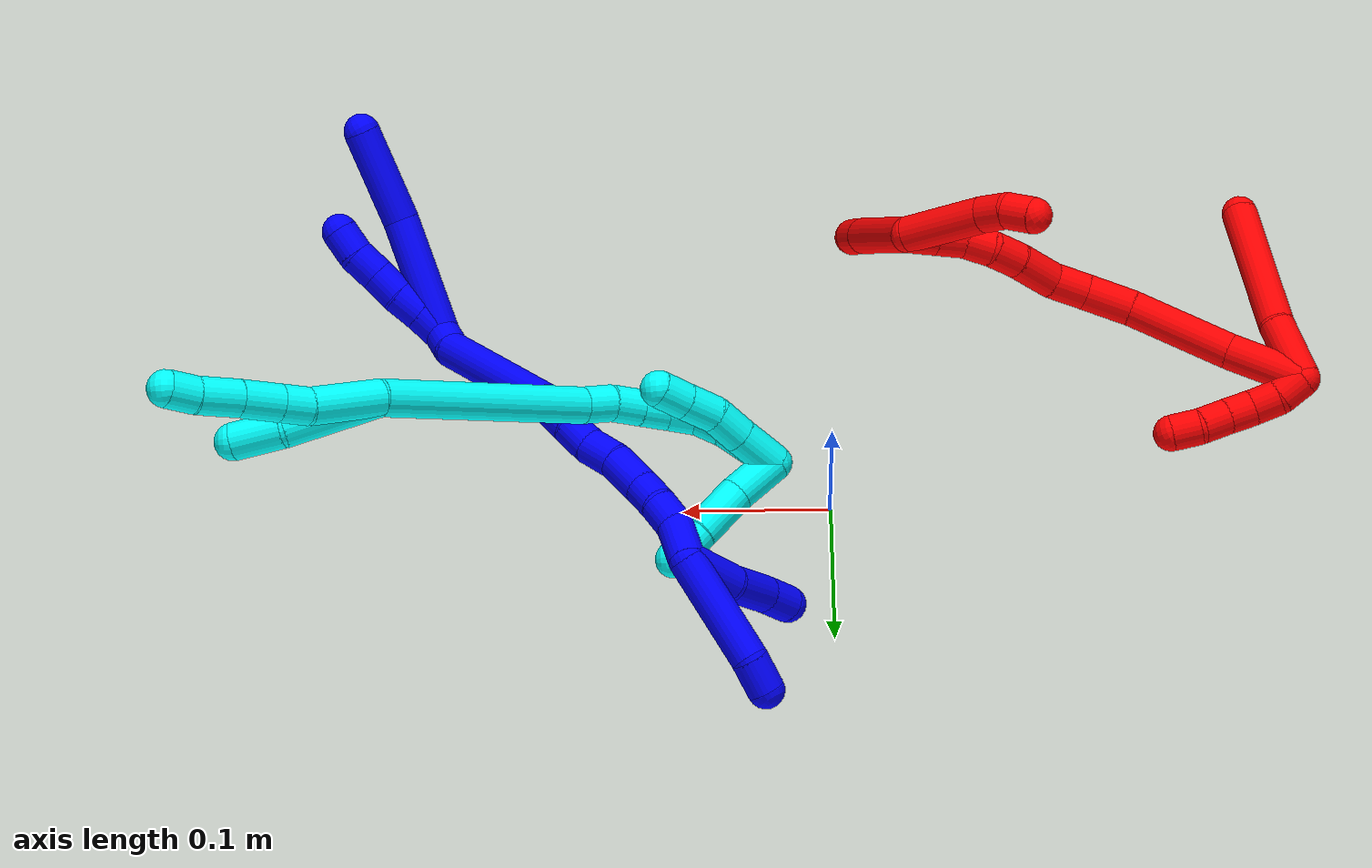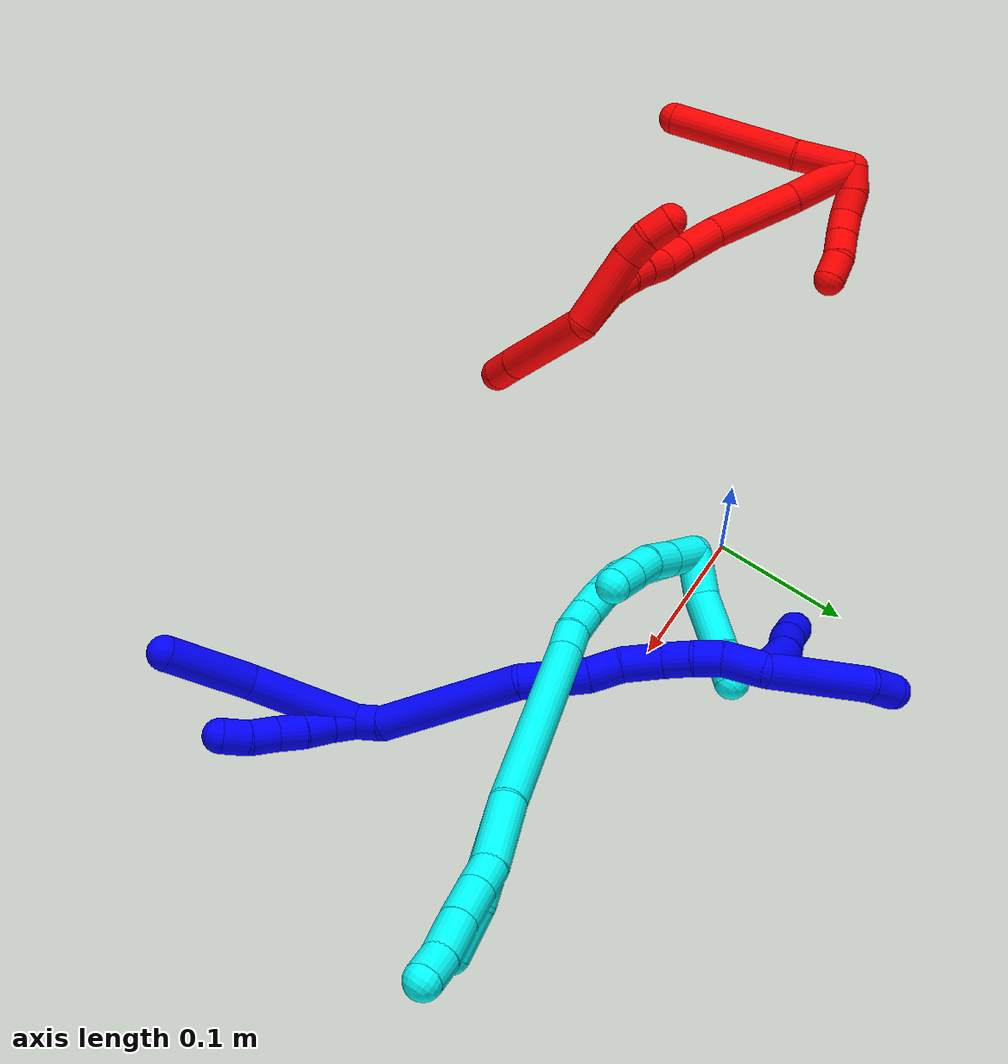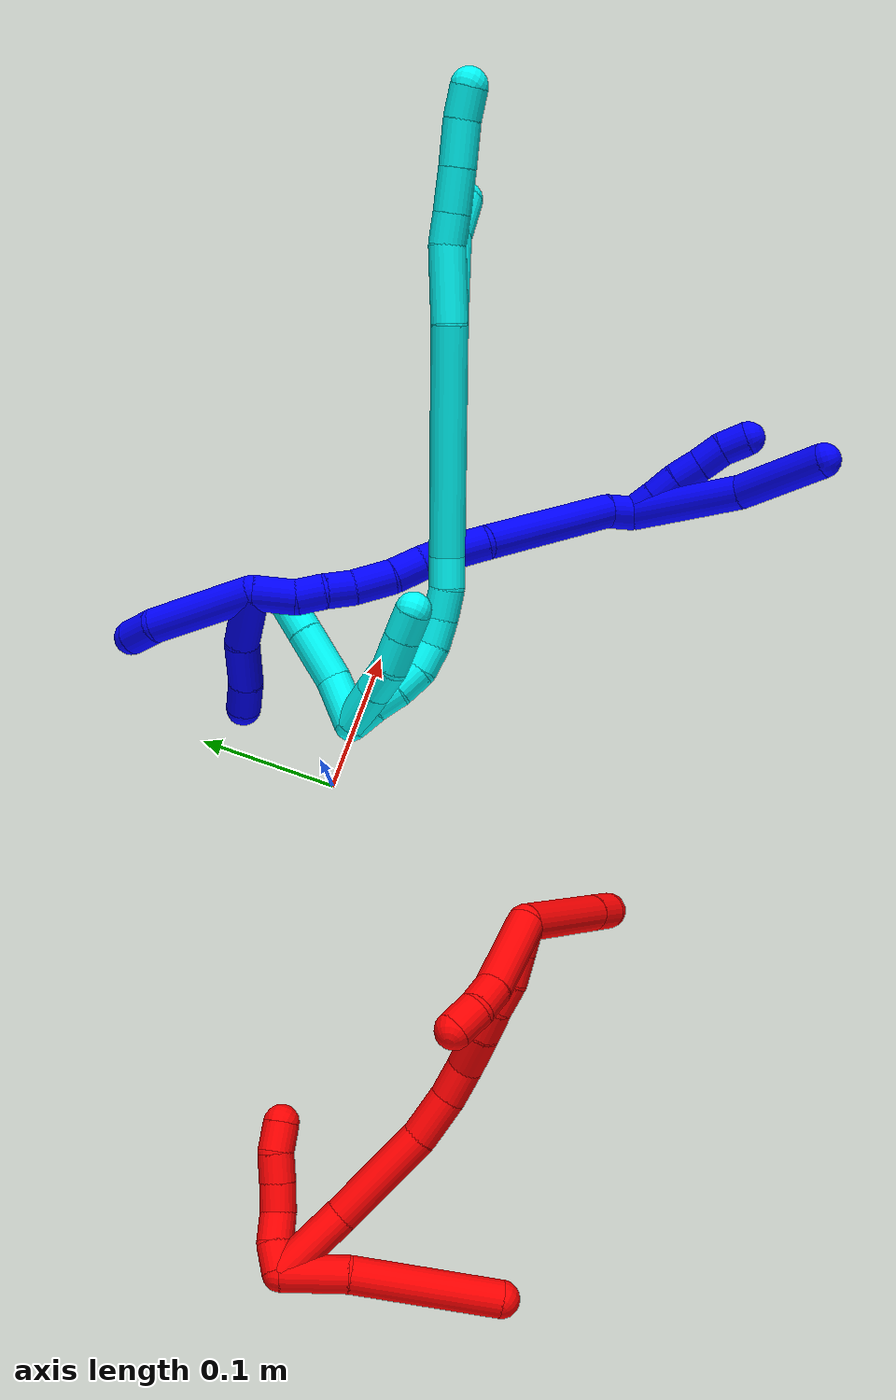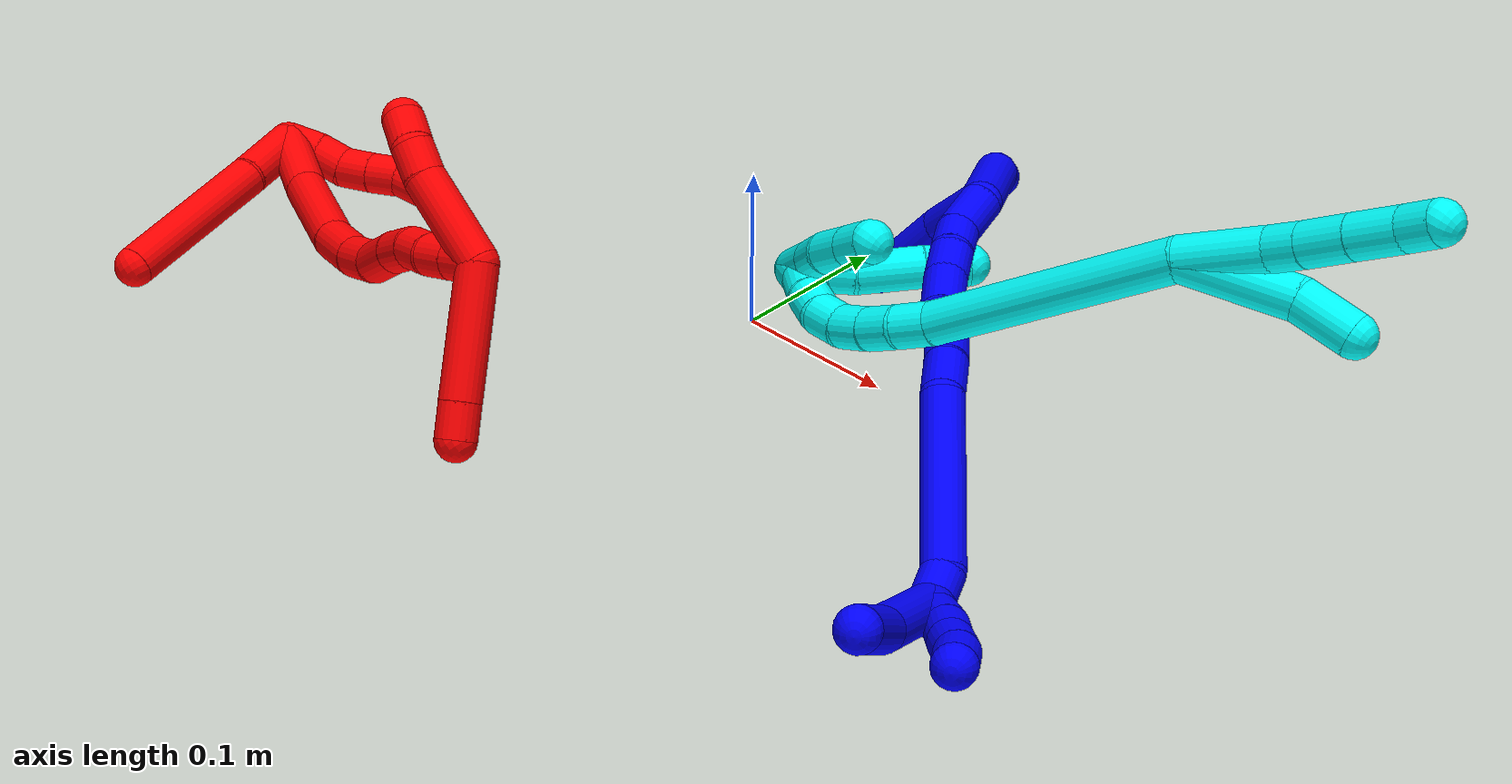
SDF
<sdf version="1.7">
 <world name="default">
  <plugin name="TubeGeneratorPlugin" filename="libtube_generator_plugin.so"/>
  <model name="photoneo_s_sensor">
   <static>1</static>
   <pose>0 0 2 1.57079 1.57079 3.14159</pose>
   <link name="link">
    <inertial><mass>0.1</mass></inertial>
    <sensor name="sensor" type="depth">
     <update_rate>30</update_rate>
     <camera>
      <horizontal_fov>1.22</horizontal_fov>
      <image><width>1920</width><height>1200</height><format>B8G8R8</format></image>
      <clip><near>0.1</near><far>4</far></clip>
      <depth_camera><output>points</output></depth_camera>
     </camera>
     <plugin name="camera_plugin" filename="libgazebo_ros_depth_camera.so">
      <baseline>0.2</baseline>
      <alwaysOn>1</alwaysOn>
      <updateRate>0.0</updateRate>
      <cameraName>camera_ir</cameraName>
      <imageTopicName>/camera/color/image_raw</imageTopicName>
      <cameraInfoTopicName>/camera/color/camera_info</cameraInfoTopicName>
      <depthImageTopicName>/camera/depth/image_raw</depthImageTopicName>
      <depthImageCameraInfoTopicName>/camera/depth/camera_info</depthImageCameraInfoTopicName>
      <pointCloudTopicName>/camera/depth/points</pointCloudTopicName>
      <frameName>fr_optical</frameName>
      <pointCloudCutoff>0.1</pointCloudCutoff>
      <pointCloudCutoffMax>2.0</pointCloudCutoffMax>
      <distortionK1>0</distortionK1>
      <distortionK2>0</distortionK2>
      <distortionK3>0</distortionK3>
      <distortionT1>0</distortionT1>
      <distortionT2>0</distortionT2>
      <CxPrime>0</CxPrime>
      <Cx>0</Cx>
      <Cy>0</Cy>
      <focalLength>0</focalLength>
      <hackBaseline>0</hackBaseline>
     </plugin>
    </sensor>
   </link>
  </model>
  <gravity>0 0 -9.8</gravity>
  <magnetic_field>6e-06 2.3e-05 -4.2e-05</magnetic_field>
  <atmosphere type="adiabatic"/>
  <physics name="default_physics" default="0" type="ode">
   <max_step_size>0.003</max_step_size>
   <real_time_factor>1</real_time_factor>
   <real_time_update_rate>1000</real_time_update_rate>
   <max_contacts>10000</max_contacts>
   <ode>
    <solver>
     <type>quick</type>
     <iters>100</iters>
     <sor>1.3</sor>
     <use_dynamic_moi_rescaling>0</use_dynamic_moi_rescaling>
    </solver>
    <constraints>
     <contact_max_correcting_vel>0</contact_max_correcting_vel>
     <contact_surface_layer>0.001</contact_surface_layer>
     <cfm>0</cfm>
     <erp>0.2</erp>
    </constraints>
   </ode>
  </physics>
  <scene><ambient>0.4 0.4 0.4 1</ambient><background>0.7 0.7 0.7 1</background><shadows>0</shadows></scene>
  <audio><device>default</device></audio>
  <spherical_coordinates>
   <surface_model>EARTH_WGS84</surface_model>
   <latitude_deg>0</latitude_deg>
   <longitude_deg>0</longitude_deg>
   <elevation>0</elevation>
   <heading_deg>0</heading_deg>
  </spherical_coordinates>
  <model name="bin">
   <static>1</static>
   <link name="bottom">
    <collision name="collision-bottom">
     <pose>0 0 -0.01 0 -0 0</pose>
     <geometry><box><size>0.8 0.6 0.02</size></box></geometry>
     <surface>
      <friction><ode><mu>100</mu><mu2>100</mu2></ode></friction>
      <contact><collide_bitmask>65535</collide_bitmask></contact>
     </surface>
    </collision>
   </link>
   <link name="west_wall">
    <collision name="collision-west_wall">
     <pose>-0.41 0 0.1 0 -0 0</pose>
     <geometry><box><size>0.02 0.6 0.2</size></box></geometry>
     <surface>
      <friction><ode><mu>100</mu><mu2>100</mu2></ode></friction>
      <contact><collide_bitmask>65535</collide_bitmask></contact>
     </surface>
    </collision>
   </link>
   <link name="east_wall">
    <collision name="collision-east_wall">
     <pose>0.41 0 0.1 0 -0 0</pose>
     <geometry><box><size>0.02 0.6 0.2</size></box></geometry>
     <surface>
      <friction><ode><mu>100</mu><mu2>100</mu2></ode></friction>
      <contact><collide_bitmask>65535</collide_bitmask></contact>
     </surface>
    </collision>
   </link>
   <link name="south_wall">
    <collision name="collision-south_wall">
     <pose>0 -0.31 0.1 0 -0 0</pose>
     <geometry><box><size>0.8 0.02 0.2</size></box></geometry>
     <surface>
      <friction><ode><mu>100</mu><mu2>100</mu2></ode></friction>
      <contact><collide_bitmask>65535</collide_bitmask></contact>
     </surface>
    </collision>
   </link>
   <link name="north_wall">
    <collision name="collision-north_wall">
     <pose>0 0.31 0.1 0 -0 0</pose>
     <geometry><box><size>0.8 0.02 0.2</size></box></geometry>
     <surface>
      <friction><ode><mu>100</mu><mu2>100</mu2></ode></friction>
      <contact><collide_bitmask>65535</collide_bitmask></contact>
     </surface>
    </collision>
   </link>
  </model>
  <model name="1">
   <static>0</static>
   <link name="1">
    <collision name="collision-cylinder-e_1_2_8">
     <pose>-0.007749 0.003835 0.040748 -0.093843 -0.187114 0.008812</pose>
     <geometry><cylinder><radius>0.0125</radius><length>0.08331</length></cylinder></geometry>
     <surface>
      <friction><ode><mu>1.16</mu><mu2>1.16</mu2><slip1>0</slip1><slip2>0</slip2></ode></friction>
      <contact><ode><kp>1e+06</kp><kd>1</kd><max_vel>0</max_vel><min_depth>0.001</min_depth></ode></contact>
     </surface>
    </collision>
    <visual name="visual-cylinder-e_1_2_8">
     <pose>-0.007749 0.003835 0.040748 -0.093843 -0.187114 0.008812</pose>
     <geometry><cylinder><radius>0.0125</radius><length>0.08331</length></cylinder></geometry>
     <material><ambient>0 0 1 1</ambient></material>
    </visual>
    <collision name="collision-cylinder-e_2_8_6">
     <pose>-0.019212 0.017314 0.113199 -0.295297 -0.111626 0.016619</pose>
     <geometry><cylinder><radius>0.0125</radius><length>0.06669</length></cylinder></geometry>
     <surface>
      <friction><ode><mu>1.16</mu><mu2>1.16</mu2><slip1>0</slip1><slip2>0</slip2></ode></friction>
      <contact><ode><kp>1e+06</kp><kd>1</kd><max_vel>0</max_vel><min_depth>0.001</min_depth></ode></contact>
     </surface>
    </collision>
    <visual name="visual-cylinder-e_2_8_6">
     <pose>-0.019212 0.017314 0.113199 -0.295297 -0.111626 0.016619</pose>
     <geometry><cylinder><radius>0.0125</radius><length>0.06669</length></cylinder></geometry>
     <material><ambient>0 0 1 1</ambient></material>
    </visual>
    <collision name="collision-cylinder-e_1_2_9">
     <pose>0.002928 0.001173 0.009489 -0.122989 0.297201 -0.018435</pose>
     <geometry><cylinder><radius>0.0125</radius><length>0.02</length></cylinder></geometry>
     <surface>
      <friction><ode><mu>1.16</mu><mu2>1.16</mu2><slip1>0</slip1><slip2>0</slip2></ode></friction>
      <contact><ode><kp>1e+06</kp><kd>1</kd><max_vel>0</max_vel><min_depth>0.001</min_depth></ode></contact>
     </surface>
    </collision>
    <visual name="visual-cylinder-e_1_2_9">
     <pose>0.002928 0.001173 0.009489 -0.122989 0.297201 -0.018435</pose>
     <geometry><cylinder><radius>0.0125</radius><length>0.02</length></cylinder></geometry>
     <material><ambient>0 0 1 1</ambient></material>
    </visual>
    <collision name="collision-cylinder-e_2_9_10">
     <pose>0.009378 0.003514 0.028265 -0.125108 0.359828 -0.022783</pose>
     <geometry><cylinder><radius>0.0125</radius><length>0.02</length></cylinder></geometry>
     <surface>
      <friction><ode><mu>1.16</mu><mu2>1.16</mu2><slip1>0</slip1><slip2>0</slip2></ode></friction>
      <contact><ode><kp>1e+06</kp><kd>1</kd><max_vel>0</max_vel><min_depth>0.001</min_depth></ode></contact>
     </surface>
    </collision>
    <visual name="visual-cylinder-e_2_9_10">
     <pose>0.009378 0.003514 0.028265 -0.125108 0.359828 -0.022783</pose>
     <geometry><cylinder><radius>0.0125</radius><length>0.02</length></cylinder></geometry>
     <material><ambient>0 0 1 1</ambient></material>
    </visual>
    <collision name="collision-cylinder-e_3_10_11">
     <pose>0.015329 0.005145 0.047241 -0.047745 0.245403 -0.005889</pose>
     <geometry><cylinder><radius>0.0125</radius><length>0.02</length></cylinder></geometry>
     <surface>
      <friction><ode><mu>1.16</mu><mu2>1.16</mu2><slip1>0</slip1><slip2>0</slip2></ode></friction>
      <contact><ode><kp>1e+06</kp><kd>1</kd><max_vel>0</max_vel><min_depth>0.001</min_depth></ode></contact>
     </surface>
    </collision>
    <visual name="visual-cylinder-e_3_10_11">
     <pose>0.015329 0.005145 0.047241 -0.047745 0.245403 -0.005889</pose>
     <geometry><cylinder><radius>0.0125</radius><length>0.02</length></cylinder></geometry>
     <material><ambient>0 0 1 1</ambient></material>
    </visual>
    <collision name="collision-cylinder-e_4_11_12">
     <pose>0.020621 0.006596 0.066461 -0.103351 0.290362 -0.015124</pose>
     <geometry><cylinder><radius>0.0125</radius><length>0.02</length></cylinder></geometry>
     <surface>
      <friction><ode><mu>1.16</mu><mu2>1.16</mu2><slip1>0</slip1><slip2>0</slip2></ode></friction>
      <contact><ode><kp>1e+06</kp><kd>1</kd><max_vel>0</max_vel><min_depth>0.001</min_depth></ode></contact>
     </surface>
    </collision>
    <visual name="visual-cylinder-e_4_11_12">
     <pose>0.020621 0.006596 0.066461 -0.103351 0.290362 -0.015124</pose>
     <geometry><cylinder><radius>0.0125</radius><length>0.02</length></cylinder></geometry>
     <material><ambient>0 0 1 1</ambient></material>
    </visual>
    <collision name="collision-cylinder-e_5_12_5">
     <pose>0.02415 0.00782 0.085966 -0.023583 0.066591 -0.000786</pose>
     <geometry><cylinder><radius>0.0125</radius><length>0.02</length></cylinder></geometry>
     <surface>
      <friction><ode><mu>1.16</mu><mu2>1.16</mu2><slip1>0</slip1><slip2>0</slip2></ode></friction>
      <contact><ode><kp>1e+06</kp><kd>1</kd><max_vel>0</max_vel><min_depth>0.001</min_depth></ode></contact>
     </surface>
    </collision>
    <visual name="visual-cylinder-e_5_12_5">
     <pose>0.02415 0.00782 0.085966 -0.023583 0.066591 -0.000786</pose>
     <geometry><cylinder><radius>0.0125</radius><length>0.02</length></cylinder></geometry>
     <material><ambient>0 0 1 1</ambient></material>
    </visual>
    <collision name="collision-cylinder-e_1_2_13">
     <pose>0.000176 0.007151 -0.007935 -2.40812 0.016469 -0.042869</pose>
     <geometry><cylinder><radius>0.0125</radius><length>0.021368</length></cylinder></geometry>
     <surface>
      <friction><ode><mu>1.16</mu><mu2>1.16</mu2><slip1>0</slip1><slip2>0</slip2></ode></friction>
      <contact><ode><kp>1e+06</kp><kd>1</kd><max_vel>0</max_vel><min_depth>0.001</min_depth></ode></contact>
     </surface>
    </collision>
    <visual name="visual-cylinder-e_1_2_13">
     <pose>0.000176 0.007151 -0.007935 -2.40812 0.016469 -0.042869</pose>
     <geometry><cylinder><radius>0.0125</radius><length>0.021368</length></cylinder></geometry>
     <material><ambient>0 0 1 1</ambient></material>
    </visual>
    <collision name="collision-cylinder-e_2_13_14">
     <pose>-0.016501 0.048567 -0.053269 -2.3999 -0.320781 0.788546</pose>
     <geometry><cylinder><radius>0.0125</radius><length>0.106896</length></cylinder></geometry>
     <surface>
      <friction><ode><mu>1.16</mu><mu2>1.16</mu2><slip1>0</slip1><slip2>0</slip2></ode></friction>
      <contact><ode><kp>1e+06</kp><kd>1</kd><max_vel>0</max_vel><min_depth>0.001</min_depth></ode></contact>
     </surface>
    </collision>
    <visual name="visual-cylinder-e_2_13_14">
     <pose>-0.016501 0.048567 -0.053269 -2.3999 -0.320781 0.788546</pose>
     <geometry><cylinder><radius>0.0125</radius><length>0.106896</length></cylinder></geometry>
     <material><ambient>0 0 1 1</ambient></material>
    </visual>
    <collision name="collision-cylinder-e_3_14_15">
     <pose>-0.035886 0.088405 -0.102948 -2.71557 -0.185663 0.812932</pose>
     <geometry><cylinder><radius>0.0125</radius><length>0.027443</length></cylinder></geometry>
     <surface>
      <friction><ode><mu>1.16</mu><mu2>1.16</mu2><slip1>0</slip1><slip2>0</slip2></ode></friction>
      <contact><ode><kp>1e+06</kp><kd>1</kd><max_vel>0</max_vel><min_depth>0.001</min_depth></ode></contact>
     </surface>
    </collision>
    <visual name="visual-cylinder-e_3_14_15">
     <pose>-0.035886 0.088405 -0.102948 -2.71557 -0.185663 0.812932</pose>
     <geometry><cylinder><radius>0.0125</radius><length>0.027443</length></cylinder></geometry>
     <material><ambient>0 0 1 1</ambient></material>
    </visual>
    <collision name="collision-cylinder-e_4_15_16">
     <pose>-0.040645 0.09693 -0.124867 -2.84442 -0.217298 1.25946</pose>
     <geometry><cylinder><radius>0.0125</radius><length>0.020647</length></cylinder></geometry>
     <surface>
      <friction><ode><mu>1.16</mu><mu2>1.16</mu2><slip1>0</slip1><slip2>0</slip2></ode></friction>
      <contact><ode><kp>1e+06</kp><kd>1</kd><max_vel>0</max_vel><min_depth>0.001</min_depth></ode></contact>
     </surface>
    </collision>
    <visual name="visual-cylinder-e_4_15_16">
     <pose>-0.040645 0.09693 -0.124867 -2.84442 -0.217298 1.25946</pose>
     <geometry><cylinder><radius>0.0125</radius><length>0.020647</length></cylinder></geometry>
     <material><ambient>0 0 1 1</ambient></material>
    </visual>
    <collision name="collision-cylinder-e_5_16_17">
     <pose>-0.047446 0.105141 -0.144212 -2.64502 -0.392908 1.3311</pose>
     <geometry><cylinder><radius>0.0125</radius><length>0.0239</length></cylinder></geometry>
     <surface>
      <friction><ode><mu>1.16</mu><mu2>1.16</mu2><slip1>0</slip1><slip2>0</slip2></ode></friction>
      <contact><ode><kp>1e+06</kp><kd>1</kd><max_vel>0</max_vel><min_depth>0.001</min_depth></ode></contact>
     </surface>
    </collision>
    <visual name="visual-cylinder-e_5_16_17">
     <pose>-0.047446 0.105141 -0.144212 -2.64502 -0.392908 1.3311</pose>
     <geometry><cylinder><radius>0.0125</radius><length>0.0239</length></cylinder></geometry>
     <material><ambient>0 0 1 1</ambient></material>
    </visual>
    <collision name="collision-cylinder-e_6_17_18">
     <pose>-0.054817 0.116387 -0.16679 -2.70625 -0.194436 0.830579</pose>
     <geometry><cylinder><radius>0.0125</radius><length>0.028938</length></cylinder></geometry>
     <surface>
      <friction><ode><mu>1.16</mu><mu2>1.16</mu2><slip1>0</slip1><slip2>0</slip2></ode></friction>
      <contact><ode><kp>1e+06</kp><kd>1</kd><max_vel>0</max_vel><min_depth>0.001</min_depth></ode></contact>
     </surface>
    </collision>
    <visual name="visual-cylinder-e_6_17_18">
     <pose>-0.054817 0.116387 -0.16679 -2.70625 -0.194436 0.830579</pose>
     <geometry><cylinder><radius>0.0125</radius><length>0.028938</length></cylinder></geometry>
     <material><ambient>0 0 1 1</ambient></material>
    </visual>
    <collision name="collision-cylinder-e_7_18_19">
     <pose>-0.058881 0.128256 -0.188024 -2.52856 -0.123427 0.385628</pose>
     <geometry><cylinder><radius>0.0125</radius><length>0.020604</length></cylinder></geometry>
     <surface>
      <friction><ode><mu>1.16</mu><mu2>1.16</mu2><slip1>0</slip1><slip2>0</slip2></ode></friction>
      <contact><ode><kp>1e+06</kp><kd>1</kd><max_vel>0</max_vel><min_depth>0.001</min_depth></ode></contact>
     </surface>
    </collision>
    <visual name="visual-cylinder-e_7_18_19">
     <pose>-0.058881 0.128256 -0.188024 -2.52856 -0.123427 0.385628</pose>
     <geometry><cylinder><radius>0.0125</radius><length>0.020604</length></cylinder></geometry>
     <material><ambient>0 0 1 1</ambient></material>
    </visual>
    <collision name="collision-cylinder-e_8_19_20">
     <pose>-0.061125 0.138035 -0.205696 -2.74519 -0.09645 0.471661</pose>
     <geometry><cylinder><radius>0.0125</radius><length>0.02028</length></cylinder></geometry>
     <surface>
      <friction><ode><mu>1.16</mu><mu2>1.16</mu2><slip1>0</slip1><slip2>0</slip2></ode></friction>
      <contact><ode><kp>1e+06</kp><kd>1</kd><max_vel>0</max_vel><min_depth>0.001</min_depth></ode></contact>
     </surface>
    </collision>
    <visual name="visual-cylinder-e_8_19_20">
     <pose>-0.061125 0.138035 -0.205696 -2.74519 -0.09645 0.471661</pose>
     <geometry><cylinder><radius>0.0125</radius><length>0.02028</length></cylinder></geometry>
     <material><ambient>0 0 1 1</ambient></material>
    </visual>
    <collision name="collision-cylinder-e_9_20_1">
     <pose>-0.05928 0.14928 -0.227731 -2.61789 0.189726 -0.682292</pose>
     <geometry><cylinder><radius>0.0125</radius><length>0.029925</length></cylinder></geometry>
     <surface>
      <friction><ode><mu>1.16</mu><mu2>1.16</mu2><slip1>0</slip1><slip2>0</slip2></ode></friction>
      <contact><ode><kp>1e+06</kp><kd>1</kd><max_vel>0</max_vel><min_depth>0.001</min_depth></ode></contact>
     </surface>
    </collision>
    <visual name="visual-cylinder-e_9_20_1">
     <pose>-0.05928 0.14928 -0.227731 -2.61789 0.189726 -0.682292</pose>
     <geometry><cylinder><radius>0.0125</radius><length>0.029925</length></cylinder></geometry>
     <material><ambient>0 0 1 1</ambient></material>
    </visual>
    <collision name="collision-cylinder-e_1_1_21">
     <pose>-0.065943 0.142955 -0.253075 2.31617 -0.471401 -1.00338</pose>
     <geometry><cylinder><radius>0.0125</radius><length>0.041769</length></cylinder></geometry>
     <surface>
      <friction><ode><mu>1.16</mu><mu2>1.16</mu2><slip1>0</slip1><slip2>0</slip2></ode></friction>
      <contact><ode><kp>1e+06</kp><kd>1</kd><max_vel>0</max_vel><min_depth>0.001</min_depth></ode></contact>
     </surface>
    </collision>
    <visual name="visual-cylinder-e_1_1_21">
     <pose>-0.065943 0.142955 -0.253075 2.31617 -0.471401 -1.00338</pose>
     <geometry><cylinder><radius>0.0125</radius><length>0.041769</length></cylinder></geometry>
     <material><ambient>0 0 1 1</ambient></material>
    </visual>
    <collision name="collision-cylinder-e_2_21_22">
     <pose>-0.083496 0.115276 -0.272693 2.03412 -0.475863 -0.747656</pose>
     <geometry><cylinder><radius>0.0125</radius><length>0.035228</length></cylinder></geometry>
     <surface>
      <friction><ode><mu>1.16</mu><mu2>1.16</mu2><slip1>0</slip1><slip2>0</slip2></ode></friction>
      <contact><ode><kp>1e+06</kp><kd>1</kd><max_vel>0</max_vel><min_depth>0.001</min_depth></ode></contact>
     </surface>
    </collision>
    <visual name="visual-cylinder-e_2_21_22">
     <pose>-0.083496 0.115276 -0.272693 2.03412 -0.475863 -0.747656</pose>
     <geometry><cylinder><radius>0.0125</radius><length>0.035228</length></cylinder></geometry>
     <material><ambient>0 0 1 1</ambient></material>
    </visual>
    <collision name="collision-cylinder-e_3_22_4">
     <pose>-0.097031 0.093154 -0.285735 2.21091 -0.495213 -0.932813</pose>
     <geometry><cylinder><radius>0.0125</radius><length>0.023003</length></cylinder></geometry>
     <surface>
      <friction><ode><mu>1.16</mu><mu2>1.16</mu2><slip1>0</slip1><slip2>0</slip2></ode></friction>
      <contact><ode><kp>1e+06</kp><kd>1</kd><max_vel>0</max_vel><min_depth>0.001</min_depth></ode></contact>
     </surface>
    </collision>
    <visual name="visual-cylinder-e_3_22_4">
     <pose>-0.097031 0.093154 -0.285735 2.21091 -0.495213 -0.932813</pose>
     <geometry><cylinder><radius>0.0125</radius><length>0.023003</length></cylinder></geometry>
     <material><ambient>0 0 1 1</ambient></material>
    </visual>
    <collision name="collision-cylinder-e_1_1_23">
     <pose>-0.057281 0.157903 -0.278724 -3.1083 -0.021482 1.14603</pose>
     <geometry><cylinder><radius>0.0125</radius><length>0.076598</length></cylinder></geometry>
     <surface>
      <friction><ode><mu>1.16</mu><mu2>1.16</mu2><slip1>0</slip1><slip2>0</slip2></ode></friction>
      <contact><ode><kp>1e+06</kp><kd>1</kd><max_vel>0</max_vel><min_depth>0.001</min_depth></ode></contact>
     </surface>
    </collision>
    <visual name="visual-cylinder-e_1_1_23">
     <pose>-0.057281 0.157903 -0.278724 -3.1083 -0.021482 1.14603</pose>
     <geometry><cylinder><radius>0.0125</radius><length>0.076598</length></cylinder></geometry>
     <material><ambient>0 0 1 1</ambient></material>
    </visual>
    <collision name="collision-cylinder-e_2_23_3">
     <pose>-0.057657 0.155897 -0.328216 2.85725 0.038172 0.265146</pose>
     <geometry><cylinder><radius>0.0125</radius><length>0.023402</length></cylinder></geometry>
     <surface>
      <friction><ode><mu>1.16</mu><mu2>1.16</mu2><slip1>0</slip1><slip2>0</slip2></ode></friction>
      <contact><ode><kp>1e+06</kp><kd>1</kd><max_vel>0</max_vel><min_depth>0.001</min_depth></ode></contact>
     </surface>
    </collision>
    <visual name="visual-cylinder-e_2_23_3">
     <pose>-0.057657 0.155897 -0.328216 2.85725 0.038172 0.265146</pose>
     <geometry><cylinder><radius>0.0125</radius><length>0.023402</length></cylinder></geometry>
     <material><ambient>0 0 1 1</ambient></material>
    </visual>
    <collision name="collision-sphere-3">
     <pose>-0.057211 0.152617 -0.339439 0 -0 0</pose>
     <geometry><sphere><radius>0.0125</radius></sphere></geometry>
     <surface>
      <friction><ode><mu>1.16</mu><mu2>1.16</mu2><slip1>0</slip1><slip2>0</slip2></ode></friction>
      <contact><ode><kp>1e+06</kp><kd>1</kd><max_vel>0</max_vel><min_depth>0.001</min_depth></ode></contact>
     </surface>
    </collision>
    <visual name="visual-sphere-3">
     <pose>-0.057211 0.152617 -0.339439 0 -0 0</pose>
     <geometry><sphere><radius>0.0125</radius></sphere></geometry>
     <material><ambient>0 0 1 1</ambient></material>
    </visual>
    <collision name="collision-sphere-23">
     <pose>-0.058104 0.159177 -0.316994 0 -0 0</pose>
     <geometry><sphere><radius>0.0125</radius></sphere></geometry>
     <surface>
      <friction><ode><mu>1.16</mu><mu2>1.16</mu2><slip1>0</slip1><slip2>0</slip2></ode></friction>
      <contact><ode><kp>1e+06</kp><kd>1</kd><max_vel>0</max_vel><min_depth>0.001</min_depth></ode></contact>
     </surface>
    </collision>
    <visual name="visual-sphere-23">
     <pose>-0.058104 0.159177 -0.316994 0 -0 0</pose>
     <geometry><sphere><radius>0.0125</radius></sphere></geometry>
     <material><ambient>0 0 1 1</ambient></material>
    </visual>
    <collision name="collision-sphere-4">
     <pose>-0.102497 0.085037 -0.291779 0 -0 0</pose>
     <geometry><sphere><radius>0.0125</radius></sphere></geometry>
     <surface>
      <friction><ode><mu>1.16</mu><mu2>1.16</mu2><slip1>0</slip1><slip2>0</slip2></ode></friction>
      <contact><ode><kp>1e+06</kp><kd>1</kd><max_vel>0</max_vel><min_depth>0.001</min_depth></ode></contact>
     </surface>
    </collision>
    <visual name="visual-sphere-4">
     <pose>-0.102497 0.085037 -0.291779 0 -0 0</pose>
     <geometry><sphere><radius>0.0125</radius></sphere></geometry>
     <material><ambient>0 0 1 1</ambient></material>
    </visual>
    <collision name="collision-sphere-22">
     <pose>-0.091566 0.10127 -0.27969 0 -0 0</pose>
     <geometry><sphere><radius>0.0125</radius></sphere></geometry>
     <surface>
      <friction><ode><mu>1.16</mu><mu2>1.16</mu2><slip1>0</slip1><slip2>0</slip2></ode></friction>
      <contact><ode><kp>1e+06</kp><kd>1</kd><max_vel>0</max_vel><min_depth>0.001</min_depth></ode></contact>
     </surface>
    </collision>
    <visual name="visual-sphere-22">
     <pose>-0.091566 0.10127 -0.27969 0 -0 0</pose>
     <geometry><sphere><radius>0.0125</radius></sphere></geometry>
     <material><ambient>0 0 1 1</ambient></material>
    </visual>
    <collision name="collision-sphere-21">
     <pose>-0.075427 0.129283 -0.265695 0 -0 0</pose>
     <geometry><sphere><radius>0.0125</radius></sphere></geometry>
     <surface>
      <friction><ode><mu>1.16</mu><mu2>1.16</mu2><slip1>0</slip1><slip2>0</slip2></ode></friction>
      <contact><ode><kp>1e+06</kp><kd>1</kd><max_vel>0</max_vel><min_depth>0.001</min_depth></ode></contact>
     </surface>
    </collision>
    <visual name="visual-sphere-21">
     <pose>-0.075427 0.129283 -0.265695 0 -0 0</pose>
     <geometry><sphere><radius>0.0125</radius></sphere></geometry>
     <material><ambient>0 0 1 1</ambient></material>
    </visual>
    <collision name="collision-sphere-1">
     <pose>-0.056458 0.156628 -0.240455 0 -0 0</pose>
     <geometry><sphere><radius>0.0125</radius></sphere></geometry>
     <surface>
      <friction><ode><mu>1.16</mu><mu2>1.16</mu2><slip1>0</slip1><slip2>0</slip2></ode></friction>
      <contact><ode><kp>1e+06</kp><kd>1</kd><max_vel>0</max_vel><min_depth>0.001</min_depth></ode></contact>
     </surface>
    </collision>
    <visual name="visual-sphere-1">
     <pose>-0.056458 0.156628 -0.240455 0 -0 0</pose>
     <geometry><sphere><radius>0.0125</radius></sphere></geometry>
     <material><ambient>0 0 1 1</ambient></material>
    </visual>
    <collision name="collision-sphere-11">
     <pose>0.017758 0.005608 0.05693 0 -0 0</pose>
     <geometry><sphere><radius>0.0125</radius></sphere></geometry>
     <surface>
      <friction><ode><mu>1.16</mu><mu2>1.16</mu2><slip1>0</slip1><slip2>0</slip2></ode></friction>
      <contact><ode><kp>1e+06</kp><kd>1</kd><max_vel>0</max_vel><min_depth>0.001</min_depth></ode></contact>
     </surface>
    </collision>
    <visual name="visual-sphere-11">
     <pose>0.017758 0.005608 0.05693 0 -0 0</pose>
     <geometry><sphere><radius>0.0125</radius></sphere></geometry>
     <material><ambient>0 0 1 1</ambient></material>
    </visual>
    <collision name="collision-sphere-10">
     <pose>0.012899 0.004682 0.037552 0 -0 0</pose>
     <geometry><sphere><radius>0.0125</radius></sphere></geometry>
     <surface>
      <friction><ode><mu>1.16</mu><mu2>1.16</mu2><slip1>0</slip1><slip2>0</slip2></ode></friction>
      <contact><ode><kp>1e+06</kp><kd>1</kd><max_vel>0</max_vel><min_depth>0.001</min_depth></ode></contact>
     </surface>
    </collision>
    <visual name="visual-sphere-10">
     <pose>0.012899 0.004682 0.037552 0 -0 0</pose>
     <geometry><sphere><radius>0.0125</radius></sphere></geometry>
     <material><ambient>0 0 1 1</ambient></material>
    </visual>
    <collision name="collision-sphere-6">
     <pose>-0.022927 0.026958 0.144902 0 -0 0</pose>
     <geometry><sphere><radius>0.0125</radius></sphere></geometry>
     <surface>
      <friction><ode><mu>1.16</mu><mu2>1.16</mu2><slip1>0</slip1><slip2>0</slip2></ode></friction>
      <contact><ode><kp>1e+06</kp><kd>1</kd><max_vel>0</max_vel><min_depth>0.001</min_depth></ode></contact>
     </surface>
    </collision>
    <visual name="visual-sphere-6">
     <pose>-0.022927 0.026958 0.144902 0 -0 0</pose>
     <geometry><sphere><radius>0.0125</radius></sphere></geometry>
     <material><ambient>0 0 1 1</ambient></material>
    </visual>
    <collision name="collision-sphere-9">
     <pose>0.005857 0.002346 0.018979 0 -0 0</pose>
     <geometry><sphere><radius>0.0125</radius></sphere></geometry>
     <surface>
      <friction><ode><mu>1.16</mu><mu2>1.16</mu2><slip1>0</slip1><slip2>0</slip2></ode></friction>
      <contact><ode><kp>1e+06</kp><kd>1</kd><max_vel>0</max_vel><min_depth>0.001</min_depth></ode></contact>
     </surface>
    </collision>
    <visual name="visual-sphere-9">
     <pose>0.005857 0.002346 0.018979 0 -0 0</pose>
     <geometry><sphere><radius>0.0125</radius></sphere></geometry>
     <material><ambient>0 0 1 1</ambient></material>
    </visual>
    <collision name="collision-sphere-2">
     <geometry><sphere><radius>0.0125</radius></sphere></geometry>
     <surface>
      <friction><ode><mu>1.16</mu><mu2>1.16</mu2><slip1>0</slip1><slip2>0</slip2></ode></friction>
      <contact><ode><kp>1e+06</kp><kd>1</kd><max_vel>0</max_vel><min_depth>0.001</min_depth></ode></contact>
     </surface>
    </collision>
    <visual name="visual-sphere-2">
     <geometry><sphere><radius>0.0125</radius></sphere></geometry>
     <material><ambient>0 0 1 1</ambient></material>
    </visual>
    <collision name="collision-sphere-19">
     <pose>-0.060149 0.134138 -0.196386 0 -0 0</pose>
     <geometry><sphere><radius>0.0125</radius></sphere></geometry>
     <surface>
      <friction><ode><mu>1.16</mu><mu2>1.16</mu2><slip1>0</slip1><slip2>0</slip2></ode></friction>
      <contact><ode><kp>1e+06</kp><kd>1</kd><max_vel>0</max_vel><min_depth>0.001</min_depth></ode></contact>
     </surface>
    </collision>
    <visual name="visual-sphere-19">
     <pose>-0.060149 0.134138 -0.196386 0 -0 0</pose>
     <geometry><sphere><radius>0.0125</radius></sphere></geometry>
     <material><ambient>0 0 1 1</ambient></material>
    </visual>
    <collision name="collision-sphere-8">
     <pose>-0.015498 0.00767 0.081496 0 -0 0</pose>
     <geometry><sphere><radius>0.0125</radius></sphere></geometry>
     <surface>
      <friction><ode><mu>1.16</mu><mu2>1.16</mu2><slip1>0</slip1><slip2>0</slip2></ode></friction>
      <contact><ode><kp>1e+06</kp><kd>1</kd><max_vel>0</max_vel><min_depth>0.001</min_depth></ode></contact>
     </surface>
    </collision>
    <visual name="visual-sphere-8">
     <pose>-0.015498 0.00767 0.081496 0 -0 0</pose>
     <geometry><sphere><radius>0.0125</radius></sphere></geometry>
     <material><ambient>0 0 1 1</ambient></material>
    </visual>
    <collision name="collision-sphere-12">
     <pose>0.023484 0.007585 0.075991 0 -0 0</pose>
     <geometry><sphere><radius>0.0125</radius></sphere></geometry>
     <surface>
      <friction><ode><mu>1.16</mu><mu2>1.16</mu2><slip1>0</slip1><slip2>0</slip2></ode></friction>
      <contact><ode><kp>1e+06</kp><kd>1</kd><max_vel>0</max_vel><min_depth>0.001</min_depth></ode></contact>
     </surface>
    </collision>
    <visual name="visual-sphere-12">
     <pose>0.023484 0.007585 0.075991 0 -0 0</pose>
     <geometry><sphere><radius>0.0125</radius></sphere></geometry>
     <material><ambient>0 0 1 1</ambient></material>
    </visual>
    <collision name="collision-sphere-5">
     <pose>0.024815 0.008055 0.095941 0 -0 0</pose>
     <geometry><sphere><radius>0.0125</radius></sphere></geometry>
     <surface>
      <friction><ode><mu>1.16</mu><mu2>1.16</mu2><slip1>0</slip1><slip2>0</slip2></ode></friction>
      <contact><ode><kp>1e+06</kp><kd>1</kd><max_vel>0</max_vel><min_depth>0.001</min_depth></ode></contact>
     </surface>
    </collision>
    <visual name="visual-sphere-5">
     <pose>0.024815 0.008055 0.095941 0 -0 0</pose>
     <geometry><sphere><radius>0.0125</radius></sphere></geometry>
     <material><ambient>0 0 1 1</ambient></material>
    </visual>
    <collision name="collision-sphere-13">
     <pose>0.000352 0.014303 -0.015871 0 -0 0</pose>
     <geometry><sphere><radius>0.0125</radius></sphere></geometry>
     <surface>
      <friction><ode><mu>1.16</mu><mu2>1.16</mu2><slip1>0</slip1><slip2>0</slip2></ode></friction>
      <contact><ode><kp>1e+06</kp><kd>1</kd><max_vel>0</max_vel><min_depth>0.001</min_depth></ode></contact>
     </surface>
    </collision>
    <visual name="visual-sphere-13">
     <pose>0.000352 0.014303 -0.015871 0 -0 0</pose>
     <geometry><sphere><radius>0.0125</radius></sphere></geometry>
     <material><ambient>0 0 1 1</ambient></material>
    </visual>
    <collision name="collision-sphere-14">
     <pose>-0.033353 0.082832 -0.090668 0 -0 0</pose>
     <geometry><sphere><radius>0.0125</radius></sphere></geometry>
     <surface>
      <friction><ode><mu>1.16</mu><mu2>1.16</mu2><slip1>0</slip1><slip2>0</slip2></ode></friction>
      <contact><ode><kp>1e+06</kp><kd>1</kd><max_vel>0</max_vel><min_depth>0.001</min_depth></ode></contact>
     </surface>
    </collision>
    <visual name="visual-sphere-14">
     <pose>-0.033353 0.082832 -0.090668 0 -0 0</pose>
     <geometry><sphere><radius>0.0125</radius></sphere></geometry>
     <material><ambient>0 0 1 1</ambient></material>
    </visual>
    <collision name="collision-sphere-15">
     <pose>-0.038419 0.093978 -0.115228 0 -0 0</pose>
     <geometry><sphere><radius>0.0125</radius></sphere></geometry>
     <surface>
      <friction><ode><mu>1.16</mu><mu2>1.16</mu2><slip1>0</slip1><slip2>0</slip2></ode></friction>
      <contact><ode><kp>1e+06</kp><kd>1</kd><max_vel>0</max_vel><min_depth>0.001</min_depth></ode></contact>
     </surface>
    </collision>
    <visual name="visual-sphere-15">
     <pose>-0.038419 0.093978 -0.115228 0 -0 0</pose>
     <geometry><sphere><radius>0.0125</radius></sphere></geometry>
     <material><ambient>0 0 1 1</ambient></material>
    </visual>
    <collision name="collision-sphere-16">
     <pose>-0.042871 0.099881 -0.134506 0 -0 0</pose>
     <geometry><sphere><radius>0.0125</radius></sphere></geometry>
     <surface>
      <friction><ode><mu>1.16</mu><mu2>1.16</mu2><slip1>0</slip1><slip2>0</slip2></ode></friction>
      <contact><ode><kp>1e+06</kp><kd>1</kd><max_vel>0</max_vel><min_depth>0.001</min_depth></ode></contact>
     </surface>
    </collision>
    <visual name="visual-sphere-16">
     <pose>-0.042871 0.099881 -0.134506 0 -0 0</pose>
     <geometry><sphere><radius>0.0125</radius></sphere></geometry>
     <material><ambient>0 0 1 1</ambient></material>
    </visual>
    <collision name="collision-sphere-17">
     <pose>-0.052021 0.1104 -0.153918 0 -0 0</pose>
     <geometry><sphere><radius>0.0125</radius></sphere></geometry>
     <surface>
      <friction><ode><mu>1.16</mu><mu2>1.16</mu2><slip1>0</slip1><slip2>0</slip2></ode></friction>
      <contact><ode><kp>1e+06</kp><kd>1</kd><max_vel>0</max_vel><min_depth>0.001</min_depth></ode></contact>
     </surface>
    </collision>
    <visual name="visual-sphere-17">
     <pose>-0.052021 0.1104 -0.153918 0 -0 0</pose>
     <geometry><sphere><radius>0.0125</radius></sphere></geometry>
     <material><ambient>0 0 1 1</ambient></material>
    </visual>
    <collision name="collision-sphere-18">
     <pose>-0.057612 0.122374 -0.179662 0 -0 0</pose>
     <geometry><sphere><radius>0.0125</radius></sphere></geometry>
     <surface>
      <friction><ode><mu>1.16</mu><mu2>1.16</mu2><slip1>0</slip1><slip2>0</slip2></ode></friction>
      <contact><ode><kp>1e+06</kp><kd>1</kd><max_vel>0</max_vel><min_depth>0.001</min_depth></ode></contact>
     </surface>
    </collision>
    <visual name="visual-sphere-18">
     <pose>-0.057612 0.122374 -0.179662 0 -0 0</pose>
     <geometry><sphere><radius>0.0125</radius></sphere></geometry>
     <material><ambient>0 0 1 1</ambient></material>
    </visual>
    <collision name="collision-sphere-20">
     <pose>-0.062102 0.141932 -0.215006 0 -0 0</pose>
     <geometry><sphere><radius>0.0125</radius></sphere></geometry>
     <surface>
      <friction><ode><mu>1.16</mu><mu2>1.16</mu2><slip1>0</slip1><slip2>0</slip2></ode></friction>
      <contact><ode><kp>1e+06</kp><kd>1</kd><max_vel>0</max_vel><min_depth>0.001</min_depth></ode></contact>
     </surface>
    </collision>
    <visual name="visual-sphere-20">
     <pose>-0.062102 0.141932 -0.215006 0 -0 0</pose>
     <geometry><sphere><radius>0.0125</radius></sphere></geometry>
     <material><ambient>0 0 1 1</ambient></material>
    </visual>
    <inertial>
     <pose>-0.032899 0.073919 -0.099318 0 -0 0</pose>
     <mass>0.75</mass>
     <inertia>
      <ixx>0.000292</ixx>
      <ixy>0</ixy>
      <ixz>0</ixz>
      <iyy>0.000132</iyy>
      <iyz>0</iyz>
      <izz>-3.8e-05</izz>
     </inertia>
    </inertial>
   </link>
   <pose>0.26413 -0.140631 0.011493 1.21667 0.206037 0.481833</pose>
  </model>
  <model name="2">
   <static>0</static>
   <link name="2">
    <collision name="collision-cylinder-e_1_2_8">
     <pose>0.01289 -0.018423 -0.005665 1.86912 0.589466 0.779825</pose>
     <geometry><cylinder><radius>0.0125</radius><length>0.046374</length></cylinder></geometry>
     <surface>
      <friction><ode><mu>1.16</mu><mu2>1.16</mu2><slip1>0</slip1><slip2>0</slip2></ode></friction>
      <contact><ode><kp>1e+06</kp><kd>1</kd><max_vel>0</max_vel><min_depth>0.001</min_depth></ode></contact>
     </surface>
    </collision>
    <visual name="visual-cylinder-e_1_2_8">
     <pose>0.01289 -0.018423 -0.005665 1.86912 0.589466 0.779825</pose>
     <geometry><cylinder><radius>0.0125</radius><length>0.046374</length></cylinder></geometry>
     <material><ambient>1 0 0 1</ambient></material>
    </visual>
    <collision name="collision-cylinder-e_2_8_6">
     <pose>0.046839 -0.082874 -0.022398 1.80678 0.418548 0.526507</pose>
     <geometry><cylinder><radius>0.0125</radius><length>0.103626</length></cylinder></geometry>
     <surface>
      <friction><ode><mu>1.16</mu><mu2>1.16</mu2><slip1>0</slip1><slip2>0</slip2></ode></friction>
      <contact><ode><kp>1e+06</kp><kd>1</kd><max_vel>0</max_vel><min_depth>0.001</min_depth></ode></contact>
     </surface>
    </collision>
    <visual name="visual-cylinder-e_2_8_6">
     <pose>0.046839 -0.082874 -0.022398 1.80678 0.418548 0.526507</pose>
     <geometry><cylinder><radius>0.0125</radius><length>0.103626</length></cylinder></geometry>
     <material><ambient>1 0 0 1</ambient></material>
    </visual>
    <collision name="collision-cylinder-e_1_2_9">
     <pose>0.000652 0.006218 -0.007804 -2.46883 0.065203 -0.185998</pose>
     <geometry><cylinder><radius>0.0125</radius><length>0.02</length></cylinder></geometry>
     <surface>
      <friction><ode><mu>1.16</mu><mu2>1.16</mu2><slip1>0</slip1><slip2>0</slip2></ode></friction>
      <contact><ode><kp>1e+06</kp><kd>1</kd><max_vel>0</max_vel><min_depth>0.001</min_depth></ode></contact>
     </surface>
    </collision>
    <visual name="visual-cylinder-e_1_2_9">
     <pose>0.000652 0.006218 -0.007804 -2.46883 0.065203 -0.185998</pose>
     <geometry><cylinder><radius>0.0125</radius><length>0.02</length></cylinder></geometry>
     <material><ambient>1 0 0 1</ambient></material>
    </visual>
    <collision name="collision-cylinder-e_2_9_10">
     <pose>0.004005 0.01654 -0.024319 -2.70128 0.273566 -1.10286</pose>
     <geometry><cylinder><radius>0.0125</radius><length>0.02</length></cylinder></geometry>
     <surface>
      <friction><ode><mu>1.16</mu><mu2>1.16</mu2><slip1>0</slip1><slip2>0</slip2></ode></friction>
      <contact><ode><kp>1e+06</kp><kd>1</kd><max_vel>0</max_vel><min_depth>0.001</min_depth></ode></contact>
     </surface>
    </collision>
    <visual name="visual-cylinder-e_2_9_10">
     <pose>0.004005 0.01654 -0.024319 -2.70128 0.273566 -1.10286</pose>
     <geometry><cylinder><radius>0.0125</radius><length>0.02</length></cylinder></geometry>
     <material><ambient>1 0 0 1</ambient></material>
    </visual>
    <collision name="collision-cylinder-e_3_10_11">
     <pose>0.010986 0.026599 -0.039828 -2.4223 0.442233 -1.07768</pose>
     <geometry><cylinder><radius>0.0125</radius><length>0.02</length></cylinder></geometry>
     <surface>
      <friction><ode><mu>1.16</mu><mu2>1.16</mu2><slip1>0</slip1><slip2>0</slip2></ode></friction>
      <contact><ode><kp>1e+06</kp><kd>1</kd><max_vel>0</max_vel><min_depth>0.001</min_depth></ode></contact>
     </surface>
    </collision>
    <visual name="visual-cylinder-e_3_10_11">
     <pose>0.010986 0.026599 -0.039828 -2.4223 0.442233 -1.07768</pose>
     <geometry><cylinder><radius>0.0125</radius><length>0.02</length></cylinder></geometry>
     <material><ambient>1 0 0 1</ambient></material>
    </visual>
    <collision name="collision-cylinder-e_4_11_12">
     <pose>0.01955 0.038903 -0.053055 -2.36231 0.442764 -1.00277</pose>
     <geometry><cylinder><radius>0.0125</radius><length>0.02</length></cylinder></geometry>
     <surface>
      <friction><ode><mu>1.16</mu><mu2>1.16</mu2><slip1>0</slip1><slip2>0</slip2></ode></friction>
      <contact><ode><kp>1e+06</kp><kd>1</kd><max_vel>0</max_vel><min_depth>0.001</min_depth></ode></contact>
     </surface>
    </collision>
    <visual name="visual-cylinder-e_4_11_12">
     <pose>0.01955 0.038903 -0.053055 -2.36231 0.442764 -1.00277</pose>
     <geometry><cylinder><radius>0.0125</radius><length>0.02</length></cylinder></geometry>
     <material><ambient>1 0 0 1</ambient></material>
    </visual>
    <collision name="collision-cylinder-e_5_12_5">
     <pose>0.028159 0.049148 -0.067614 -2.69488 0.447271 -1.57209</pose>
     <geometry><cylinder><radius>0.0125</radius><length>0.02</length></cylinder></geometry>
     <surface>
      <friction><ode><mu>1.16</mu><mu2>1.16</mu2><slip1>0</slip1><slip2>0</slip2></ode></friction>
      <contact><ode><kp>1e+06</kp><kd>1</kd><max_vel>0</max_vel><min_depth>0.001</min_depth></ode></contact>
     </surface>
    </collision>
    <visual name="visual-cylinder-e_5_12_5">
     <pose>0.028159 0.049148 -0.067614 -2.69488 0.447271 -1.57209</pose>
     <geometry><cylinder><radius>0.0125</radius><length>0.02</length></cylinder></geometry>
     <material><ambient>1 0 0 1</ambient></material>
    </visual>
    <collision name="collision-cylinder-e_1_2_13">
     <pose>0.01806 -0.005789 -0.019329 2.85058 0.730063 2.40926</pose>
     <geometry><cylinder><radius>0.0125</radius><length>0.054159</length></cylinder></geometry>
     <surface>
      <friction><ode><mu>1.16</mu><mu2>1.16</mu2><slip1>0</slip1><slip2>0</slip2></ode></friction>
      <contact><ode><kp>1e+06</kp><kd>1</kd><max_vel>0</max_vel><min_depth>0.001</min_depth></ode></contact>
     </surface>
    </collision>
    <visual name="visual-cylinder-e_1_2_13">
     <pose>0.01806 -0.005789 -0.019329 2.85058 0.730063 2.40926</pose>
     <geometry><cylinder><radius>0.0125</radius><length>0.054159</length></cylinder></geometry>
     <material><ambient>1 0 0 1</ambient></material>
    </visual>
    <collision name="collision-cylinder-e_2_13_14">
     <pose>0.064548 -0.016688 -0.061468 2.92123 0.882662 2.68153</pose>
     <geometry><cylinder><radius>0.0125</radius><length>0.073607</length></cylinder></geometry>
     <surface>
      <friction><ode><mu>1.16</mu><mu2>1.16</mu2><slip1>0</slip1><slip2>0</slip2></ode></friction>
      <contact><ode><kp>1e+06</kp><kd>1</kd><max_vel>0</max_vel><min_depth>0.001</min_depth></ode></contact>
     </surface>
    </collision>
    <visual name="visual-cylinder-e_2_13_14">
     <pose>0.064548 -0.016688 -0.061468 2.92123 0.882662 2.68153</pose>
     <geometry><cylinder><radius>0.0125</radius><length>0.073607</length></cylinder></geometry>
     <material><ambient>1 0 0 1</ambient></material>
    </visual>
    <collision name="collision-cylinder-e_3_14_15">
     <pose>0.106571 -0.021073 -0.094117 -3.06811 0.942954 -2.99765</pose>
     <geometry><cylinder><radius>0.0125</radius><length>0.033598</length></cylinder></geometry>
     <surface>
      <friction><ode><mu>1.16</mu><mu2>1.16</mu2><slip1>0</slip1><slip2>0</slip2></ode></friction>
      <contact><ode><kp>1e+06</kp><kd>1</kd><max_vel>0</max_vel><min_depth>0.001</min_depth></ode></contact>
     </surface>
    </collision>
    <visual name="visual-cylinder-e_3_14_15">
     <pose>0.106571 -0.021073 -0.094117 -3.06811 0.942954 -2.99765</pose>
     <geometry><cylinder><radius>0.0125</radius><length>0.033598</length></cylinder></geometry>
     <material><ambient>1 0 0 1</ambient></material>
    </visual>
    <collision name="collision-cylinder-e_4_15_16">
     <pose>0.131028 -0.018019 -0.110101 -2.77915 1.02685 -2.51321</pose>
     <geometry><cylinder><radius>0.0125</radius><length>0.025386</length></cylinder></geometry>
     <surface>
      <friction><ode><mu>1.16</mu><mu2>1.16</mu2><slip1>0</slip1><slip2>0</slip2></ode></friction>
      <contact><ode><kp>1e+06</kp><kd>1</kd><max_vel>0</max_vel><min_depth>0.001</min_depth></ode></contact>
     </surface>
    </collision>
    <visual name="visual-cylinder-e_4_15_16">
     <pose>0.131028 -0.018019 -0.110101 -2.77915 1.02685 -2.51321</pose>
     <geometry><cylinder><radius>0.0125</radius><length>0.025386</length></cylinder></geometry>
     <material><ambient>1 0 0 1</ambient></material>
    </visual>
    <collision name="collision-cylinder-e_5_16_17">
     <pose>0.156436 -0.011328 -0.118911 -2.11975 1.23281 -1.80288</pose>
     <geometry><cylinder><radius>0.0125</radius><length>0.030839</length></cylinder></geometry>
     <surface>
      <friction><ode><mu>1.16</mu><mu2>1.16</mu2><slip1>0</slip1><slip2>0</slip2></ode></friction>
      <contact><ode><kp>1e+06</kp><kd>1</kd><max_vel>0</max_vel><min_depth>0.001</min_depth></ode></contact>
     </surface>
    </collision>
    <visual name="visual-cylinder-e_5_16_17">
     <pose>0.156436 -0.011328 -0.118911 -2.11975 1.23281 -1.80288</pose>
     <geometry><cylinder><radius>0.0125</radius><length>0.030839</length></cylinder></geometry>
     <material><ambient>1 0 0 1</ambient></material>
    </visual>
    <collision name="collision-cylinder-e_6_17_18">
     <pose>0.180973 -0.003749 -0.124605 -2.32566 1.15447 -1.96971</pose>
     <geometry><cylinder><radius>0.0125</radius><length>0.021845</length></cylinder></geometry>
     <surface>
      <friction><ode><mu>1.16</mu><mu2>1.16</mu2><slip1>0</slip1><slip2>0</slip2></ode></friction>
      <contact><ode><kp>1e+06</kp><kd>1</kd><max_vel>0</max_vel><min_depth>0.001</min_depth></ode></contact>
     </surface>
    </collision>
    <visual name="visual-cylinder-e_6_17_18">
     <pose>0.180973 -0.003749 -0.124605 -2.32566 1.15447 -1.96971</pose>
     <geometry><cylinder><radius>0.0125</radius><length>0.021845</length></cylinder></geometry>
     <material><ambient>1 0 0 1</ambient></material>
    </visual>
    <collision name="collision-cylinder-e_7_18_19">
     <pose>0.19929 0.001146 -0.132999 -2.83854 0.976876 -2.58195</pose>
     <geometry><cylinder><radius>0.0125</radius><length>0.020097</length></cylinder></geometry>
     <surface>
      <friction><ode><mu>1.16</mu><mu2>1.16</mu2><slip1>0</slip1><slip2>0</slip2></ode></friction>
      <contact><ode><kp>1e+06</kp><kd>1</kd><max_vel>0</max_vel><min_depth>0.001</min_depth></ode></contact>
     </surface>
    </collision>
    <visual name="visual-cylinder-e_7_18_19">
     <pose>0.19929 0.001146 -0.132999 -2.83854 0.976876 -2.58195</pose>
     <geometry><cylinder><radius>0.0125</radius><length>0.020097</length></cylinder></geometry>
     <material><ambient>1 0 0 1</ambient></material>
    </visual>
    <collision name="collision-cylinder-e_8_19_20">
     <pose>0.215155 0.00671 -0.144034 -2.54065 0.831544 -1.91772</pose>
     <geometry><cylinder><radius>0.0125</radius><length>0.020399</length></cylinder></geometry>
     <surface>
      <friction><ode><mu>1.16</mu><mu2>1.16</mu2><slip1>0</slip1><slip2>0</slip2></ode></friction>
      <contact><ode><kp>1e+06</kp><kd>1</kd><max_vel>0</max_vel><min_depth>0.001</min_depth></ode></contact>
     </surface>
    </collision>
    <visual name="visual-cylinder-e_8_19_20">
     <pose>0.215155 0.00671 -0.144034 -2.54065 0.831544 -1.91772</pose>
     <geometry><cylinder><radius>0.0125</radius><length>0.020399</length></cylinder></geometry>
     <material><ambient>1 0 0 1</ambient></material>
    </visual>
    <collision name="collision-cylinder-e_9_20_1">
     <pose>0.230149 0.014481 -0.155178 -2.5246 0.837687 -1.89906</pose>
     <geometry><cylinder><radius>0.0125</radius><length>0.020069</length></cylinder></geometry>
     <surface>
      <friction><ode><mu>1.16</mu><mu2>1.16</mu2><slip1>0</slip1><slip2>0</slip2></ode></friction>
      <contact><ode><kp>1e+06</kp><kd>1</kd><max_vel>0</max_vel><min_depth>0.001</min_depth></ode></contact>
     </surface>
    </collision>
    <visual name="visual-cylinder-e_9_20_1">
     <pose>0.230149 0.014481 -0.155178 -2.5246 0.837687 -1.89906</pose>
     <geometry><cylinder><radius>0.0125</radius><length>0.020069</length></cylinder></geometry>
     <material><ambient>1 0 0 1</ambient></material>
    </visual>
    <collision name="collision-cylinder-e_1_1_21">
     <pose>0.232653 -0.005774 -0.191178 2.47244 -0.126596 -0.360676</pose>
     <geometry><cylinder><radius>0.0125</radius><length>0.078457</length></cylinder></geometry>
     <surface>
      <friction><ode><mu>1.16</mu><mu2>1.16</mu2><slip1>0</slip1><slip2>0</slip2></ode></friction>
      <contact><ode><kp>1e+06</kp><kd>1</kd><max_vel>0</max_vel><min_depth>0.001</min_depth></ode></contact>
     </surface>
    </collision>
    <visual name="visual-cylinder-e_1_1_21">
     <pose>0.232653 -0.005774 -0.191178 2.47244 -0.126596 -0.360676</pose>
     <geometry><cylinder><radius>0.0125</radius><length>0.078457</length></cylinder></geometry>
     <material><ambient>1 0 0 1</ambient></material>
    </visual>
    <collision name="collision-cylinder-e_2_21_4">
     <pose>0.226075 -0.036436 -0.230117 2.48234 -0.151426 -0.436414</pose>
     <geometry><cylinder><radius>0.0125</radius><length>0.021543</length></cylinder></geometry>
     <surface>
      <friction><ode><mu>1.16</mu><mu2>1.16</mu2><slip1>0</slip1><slip2>0</slip2></ode></friction>
      <contact><ode><kp>1e+06</kp><kd>1</kd><max_vel>0</max_vel><min_depth>0.001</min_depth></ode></contact>
     </surface>
    </collision>
    <visual name="visual-cylinder-e_2_21_4">
     <pose>0.226075 -0.036436 -0.230117 2.48234 -0.151426 -0.436414</pose>
     <geometry><cylinder><radius>0.0125</radius><length>0.021543</length></cylinder></geometry>
     <material><ambient>1 0 0 1</ambient></material>
    </visual>
    <collision name="collision-cylinder-e_1_1_22">
     <pose>0.232633 0.019221 -0.131613 -0.029426 -0.169492 0.0025</pose>
     <geometry><cylinder><radius>0.0125</radius><length>0.058956</length></cylinder></geometry>
     <surface>
      <friction><ode><mu>1.16</mu><mu2>1.16</mu2><slip1>0</slip1><slip2>0</slip2></ode></friction>
      <contact><ode><kp>1e+06</kp><kd>1</kd><max_vel>0</max_vel><min_depth>0.001</min_depth></ode></contact>
     </surface>
    </collision>
    <visual name="visual-cylinder-e_1_1_22">
     <pose>0.232633 0.019221 -0.131613 -0.029426 -0.169492 0.0025</pose>
     <geometry><cylinder><radius>0.0125</radius><length>0.058956</length></cylinder></geometry>
     <material><ambient>1 0 0 1</ambient></material>
    </visual>
    <collision name="collision-cylinder-e_2_22_23">
     <pose>0.225956 0.022167 -0.09264 -0.207587 -0.166462 0.01738</pose>
     <geometry><cylinder><radius>0.0125</radius><length>0.020579</length></cylinder></geometry>
     <surface>
      <friction><ode><mu>1.16</mu><mu2>1.16</mu2><slip1>0</slip1><slip2>0</slip2></ode></friction>
      <contact><ode><kp>1e+06</kp><kd>1</kd><max_vel>0</max_vel><min_depth>0.001</min_depth></ode></contact>
     </surface>
    </collision>
    <visual name="visual-cylinder-e_2_22_23">
     <pose>0.225956 0.022167 -0.09264 -0.207587 -0.166462 0.01738</pose>
     <geometry><cylinder><radius>0.0125</radius><length>0.020579</length></cylinder></geometry>
     <material><ambient>1 0 0 1</ambient></material>
    </visual>
    <collision name="collision-cylinder-e_3_23_3">
     <pose>0.219727 0.027012 -0.073956 -0.304782 -0.458013 0.071568</pose>
     <geometry><cylinder><radius>0.0125</radius><length>0.020465</length></cylinder></geometry>
     <surface>
      <friction><ode><mu>1.16</mu><mu2>1.16</mu2><slip1>0</slip1><slip2>0</slip2></ode></friction>
      <contact><ode><kp>1e+06</kp><kd>1</kd><max_vel>0</max_vel><min_depth>0.001</min_depth></ode></contact>
     </surface>
    </collision>
    <visual name="visual-cylinder-e_3_23_3">
     <pose>0.219727 0.027012 -0.073956 -0.304782 -0.458013 0.071568</pose>
     <geometry><cylinder><radius>0.0125</radius><length>0.020465</length></cylinder></geometry>
     <material><ambient>1 0 0 1</ambient></material>
    </visual>
    <collision name="collision-sphere-3">
     <pose>0.215202 0.029767 -0.065201 0 -0 0</pose>
     <geometry><sphere><radius>0.0125</radius></sphere></geometry>
     <surface>
      <friction><ode><mu>1.16</mu><mu2>1.16</mu2><slip1>0</slip1><slip2>0</slip2></ode></friction>
      <contact><ode><kp>1e+06</kp><kd>1</kd><max_vel>0</max_vel><min_depth>0.001</min_depth></ode></contact>
     </surface>
    </collision>
    <visual name="visual-sphere-3">
     <pose>0.215202 0.029767 -0.065201 0 -0 0</pose>
     <geometry><sphere><radius>0.0125</radius></sphere></geometry>
     <material><ambient>1 0 0 1</ambient></material>
    </visual>
    <collision name="collision-sphere-23">
     <pose>0.224251 0.024258 -0.082711 0 -0 0</pose>
     <geometry><sphere><radius>0.0125</radius></sphere></geometry>
     <surface>
      <friction><ode><mu>1.16</mu><mu2>1.16</mu2><slip1>0</slip1><slip2>0</slip2></ode></friction>
      <contact><ode><kp>1e+06</kp><kd>1</kd><max_vel>0</max_vel><min_depth>0.001</min_depth></ode></contact>
     </surface>
    </collision>
    <visual name="visual-sphere-23">
     <pose>0.224251 0.024258 -0.082711 0 -0 0</pose>
     <geometry><sphere><radius>0.0125</radius></sphere></geometry>
     <material><ambient>1 0 0 1</ambient></material>
    </visual>
    <collision name="collision-sphere-22">
     <pose>0.227661 0.020075 -0.10257 0 -0 0</pose>
     <geometry><sphere><radius>0.0125</radius></sphere></geometry>
     <surface>
      <friction><ode><mu>1.16</mu><mu2>1.16</mu2><slip1>0</slip1><slip2>0</slip2></ode></friction>
      <contact><ode><kp>1e+06</kp><kd>1</kd><max_vel>0</max_vel><min_depth>0.001</min_depth></ode></contact>
     </surface>
    </collision>
    <visual name="visual-sphere-22">
     <pose>0.227661 0.020075 -0.10257 0 -0 0</pose>
     <geometry><sphere><radius>0.0125</radius></sphere></geometry>
     <material><ambient>1 0 0 1</ambient></material>
    </visual>
    <collision name="collision-sphere-4">
     <pose>0.22445 -0.042958 -0.238534 0 -0 0</pose>
     <geometry><sphere><radius>0.0125</radius></sphere></geometry>
     <surface>
      <friction><ode><mu>1.16</mu><mu2>1.16</mu2><slip1>0</slip1><slip2>0</slip2></ode></friction>
      <contact><ode><kp>1e+06</kp><kd>1</kd><max_vel>0</max_vel><min_depth>0.001</min_depth></ode></contact>
     </surface>
    </collision>
    <visual name="visual-sphere-4">
     <pose>0.22445 -0.042958 -0.238534 0 -0 0</pose>
     <geometry><sphere><radius>0.0125</radius></sphere></geometry>
     <material><ambient>1 0 0 1</ambient></material>
    </visual>
    <collision name="collision-sphere-21">
     <pose>0.2277 -0.029914 -0.2217 0 -0 0</pose>
     <geometry><sphere><radius>0.0125</radius></sphere></geometry>
     <surface>
      <friction><ode><mu>1.16</mu><mu2>1.16</mu2><slip1>0</slip1><slip2>0</slip2></ode></friction>
      <contact><ode><kp>1e+06</kp><kd>1</kd><max_vel>0</max_vel><min_depth>0.001</min_depth></ode></contact>
     </surface>
    </collision>
    <visual name="visual-sphere-21">
     <pose>0.2277 -0.029914 -0.2217 0 -0 0</pose>
     <geometry><sphere><radius>0.0125</radius></sphere></geometry>
     <material><ambient>1 0 0 1</ambient></material>
    </visual>
    <collision name="collision-sphere-1">
     <pose>0.237606 0.018366 -0.160655 0 -0 0</pose>
     <geometry><sphere><radius>0.0125</radius></sphere></geometry>
     <surface>
      <friction><ode><mu>1.16</mu><mu2>1.16</mu2><slip1>0</slip1><slip2>0</slip2></ode></friction>
      <contact><ode><kp>1e+06</kp><kd>1</kd><max_vel>0</max_vel><min_depth>0.001</min_depth></ode></contact>
     </surface>
    </collision>
    <visual name="visual-sphere-1">
     <pose>0.237606 0.018366 -0.160655 0 -0 0</pose>
     <geometry><sphere><radius>0.0125</radius></sphere></geometry>
     <material><ambient>1 0 0 1</ambient></material>
    </visual>
    <collision name="collision-sphere-11">
     <pose>0.015266 0.032553 -0.046627 0 -0 0</pose>
     <geometry><sphere><radius>0.0125</radius></sphere></geometry>
     <surface>
      <friction><ode><mu>1.16</mu><mu2>1.16</mu2><slip1>0</slip1><slip2>0</slip2></ode></friction>
      <contact><ode><kp>1e+06</kp><kd>1</kd><max_vel>0</max_vel><min_depth>0.001</min_depth></ode></contact>
     </surface>
    </collision>
    <visual name="visual-sphere-11">
     <pose>0.015266 0.032553 -0.046627 0 -0 0</pose>
     <geometry><sphere><radius>0.0125</radius></sphere></geometry>
     <material><ambient>1 0 0 1</ambient></material>
    </visual>
    <collision name="collision-sphere-10">
     <pose>0.006706 0.020644 -0.033028 0 -0 0</pose>
     <geometry><sphere><radius>0.0125</radius></sphere></geometry>
     <surface>
      <friction><ode><mu>1.16</mu><mu2>1.16</mu2><slip1>0</slip1><slip2>0</slip2></ode></friction>
      <contact><ode><kp>1e+06</kp><kd>1</kd><max_vel>0</max_vel><min_depth>0.001</min_depth></ode></contact>
     </surface>
    </collision>
    <visual name="visual-sphere-10">
     <pose>0.006706 0.020644 -0.033028 0 -0 0</pose>
     <geometry><sphere><radius>0.0125</radius></sphere></geometry>
     <material><ambient>1 0 0 1</ambient></material>
    </visual>
    <collision name="collision-sphere-6">
     <pose>0.067897 -0.128902 -0.033466 0 -0 0</pose>
     <geometry><sphere><radius>0.0125</radius></sphere></geometry>
     <surface>
      <friction><ode><mu>1.16</mu><mu2>1.16</mu2><slip1>0</slip1><slip2>0</slip2></ode></friction>
      <contact><ode><kp>1e+06</kp><kd>1</kd><max_vel>0</max_vel><min_depth>0.001</min_depth></ode></contact>
     </surface>
    </collision>
    <visual name="visual-sphere-6">
     <pose>0.067897 -0.128902 -0.033466 0 -0 0</pose>
     <geometry><sphere><radius>0.0125</radius></sphere></geometry>
     <material><ambient>1 0 0 1</ambient></material>
    </visual>
    <collision name="collision-sphere-9">
     <pose>0.001303 0.012436 -0.015609 0 -0 0</pose>
     <geometry><sphere><radius>0.0125</radius></sphere></geometry>
     <surface>
      <friction><ode><mu>1.16</mu><mu2>1.16</mu2><slip1>0</slip1><slip2>0</slip2></ode></friction>
      <contact><ode><kp>1e+06</kp><kd>1</kd><max_vel>0</max_vel><min_depth>0.001</min_depth></ode></contact>
     </surface>
    </collision>
    <visual name="visual-sphere-9">
     <pose>0.001303 0.012436 -0.015609 0 -0 0</pose>
     <geometry><sphere><radius>0.0125</radius></sphere></geometry>
     <material><ambient>1 0 0 1</ambient></material>
    </visual>
    <collision name="collision-sphere-2">
     <geometry><sphere><radius>0.0125</radius></sphere></geometry>
     <surface>
      <friction><ode><mu>1.16</mu><mu2>1.16</mu2><slip1>0</slip1><slip2>0</slip2></ode></friction>
      <contact><ode><kp>1e+06</kp><kd>1</kd><max_vel>0</max_vel><min_depth>0.001</min_depth></ode></contact>
     </surface>
    </collision>
    <visual name="visual-sphere-2">
     <geometry><sphere><radius>0.0125</radius></sphere></geometry>
     <material><ambient>1 0 0 1</ambient></material>
    </visual>
    <collision name="collision-sphere-19">
     <pose>0.207618 0.002824 -0.138366 0 -0 0</pose>
     <geometry><sphere><radius>0.0125</radius></sphere></geometry>
     <surface>
      <friction><ode><mu>1.16</mu><mu2>1.16</mu2><slip1>0</slip1><slip2>0</slip2></ode></friction>
      <contact><ode><kp>1e+06</kp><kd>1</kd><max_vel>0</max_vel><min_depth>0.001</min_depth></ode></contact>
     </surface>
    </collision>
    <visual name="visual-sphere-19">
     <pose>0.207618 0.002824 -0.138366 0 -0 0</pose>
     <geometry><sphere><radius>0.0125</radius></sphere></geometry>
     <material><ambient>1 0 0 1</ambient></material>
    </visual>
    <collision name="collision-sphere-8">
     <pose>0.02578 -0.036845 -0.01133 0 -0 0</pose>
     <geometry><sphere><radius>0.0125</radius></sphere></geometry>
     <surface>
      <friction><ode><mu>1.16</mu><mu2>1.16</mu2><slip1>0</slip1><slip2>0</slip2></ode></friction>
      <contact><ode><kp>1e+06</kp><kd>1</kd><max_vel>0</max_vel><min_depth>0.001</min_depth></ode></contact>
     </surface>
    </collision>
    <visual name="visual-sphere-8">
     <pose>0.02578 -0.036845 -0.01133 0 -0 0</pose>
     <geometry><sphere><radius>0.0125</radius></sphere></geometry>
     <material><ambient>1 0 0 1</ambient></material>
    </visual>
    <collision name="collision-sphere-12">
     <pose>0.023834 0.045253 -0.059483 0 -0 0</pose>
     <geometry><sphere><radius>0.0125</radius></sphere></geometry>
     <surface>
      <friction><ode><mu>1.16</mu><mu2>1.16</mu2><slip1>0</slip1><slip2>0</slip2></ode></friction>
      <contact><ode><kp>1e+06</kp><kd>1</kd><max_vel>0</max_vel><min_depth>0.001</min_depth></ode></contact>
     </surface>
    </collision>
    <visual name="visual-sphere-12">
     <pose>0.023834 0.045253 -0.059483 0 -0 0</pose>
     <geometry><sphere><radius>0.0125</radius></sphere></geometry>
     <material><ambient>1 0 0 1</ambient></material>
    </visual>
    <collision name="collision-sphere-5">
     <pose>0.032485 0.053043 -0.075746 0 -0 0</pose>
     <geometry><sphere><radius>0.0125</radius></sphere></geometry>
     <surface>
      <friction><ode><mu>1.16</mu><mu2>1.16</mu2><slip1>0</slip1><slip2>0</slip2></ode></friction>
      <contact><ode><kp>1e+06</kp><kd>1</kd><max_vel>0</max_vel><min_depth>0.001</min_depth></ode></contact>
     </surface>
    </collision>
    <visual name="visual-sphere-5">
     <pose>0.032485 0.053043 -0.075746 0 -0 0</pose>
     <geometry><sphere><radius>0.0125</radius></sphere></geometry>
     <material><ambient>1 0 0 1</ambient></material>
    </visual>
    <collision name="collision-sphere-13">
     <pose>0.03612 -0.011579 -0.038659 0 -0 0</pose>
     <geometry><sphere><radius>0.0125</radius></sphere></geometry>
     <surface>
      <friction><ode><mu>1.16</mu><mu2>1.16</mu2><slip1>0</slip1><slip2>0</slip2></ode></friction>
      <contact><ode><kp>1e+06</kp><kd>1</kd><max_vel>0</max_vel><min_depth>0.001</min_depth></ode></contact>
     </surface>
    </collision>
    <visual name="visual-sphere-13">
     <pose>0.03612 -0.011579 -0.038659 0 -0 0</pose>
     <geometry><sphere><radius>0.0125</radius></sphere></geometry>
     <material><ambient>1 0 0 1</ambient></material>
    </visual>
    <collision name="collision-sphere-14">
     <pose>0.092976 -0.021797 -0.084276 0 -0 0</pose>
     <geometry><sphere><radius>0.0125</radius></sphere></geometry>
     <surface>
      <friction><ode><mu>1.16</mu><mu2>1.16</mu2><slip1>0</slip1><slip2>0</slip2></ode></friction>
      <contact><ode><kp>1e+06</kp><kd>1</kd><max_vel>0</max_vel><min_depth>0.001</min_depth></ode></contact>
     </surface>
    </collision>
    <visual name="visual-sphere-14">
     <pose>0.092976 -0.021797 -0.084276 0 -0 0</pose>
     <geometry><sphere><radius>0.0125</radius></sphere></geometry>
     <material><ambient>1 0 0 1</ambient></material>
    </visual>
    <collision name="collision-sphere-15">
     <pose>0.120167 -0.020348 -0.103958 0 -0 0</pose>
     <geometry><sphere><radius>0.0125</radius></sphere></geometry>
     <surface>
      <friction><ode><mu>1.16</mu><mu2>1.16</mu2><slip1>0</slip1><slip2>0</slip2></ode></friction>
      <contact><ode><kp>1e+06</kp><kd>1</kd><max_vel>0</max_vel><min_depth>0.001</min_depth></ode></contact>
     </surface>
    </collision>
    <visual name="visual-sphere-15">
     <pose>0.120167 -0.020348 -0.103958 0 -0 0</pose>
     <geometry><sphere><radius>0.0125</radius></sphere></geometry>
     <material><ambient>1 0 0 1</ambient></material>
    </visual>
    <collision name="collision-sphere-16">
     <pose>0.141889 -0.01569 -0.116243 0 -0 0</pose>
     <geometry><sphere><radius>0.0125</radius></sphere></geometry>
     <surface>
      <friction><ode><mu>1.16</mu><mu2>1.16</mu2><slip1>0</slip1><slip2>0</slip2></ode></friction>
      <contact><ode><kp>1e+06</kp><kd>1</kd><max_vel>0</max_vel><min_depth>0.001</min_depth></ode></contact>
     </surface>
    </collision>
    <visual name="visual-sphere-16">
     <pose>0.141889 -0.01569 -0.116243 0 -0 0</pose>
     <geometry><sphere><radius>0.0125</radius></sphere></geometry>
     <material><ambient>1 0 0 1</ambient></material>
    </visual>
    <collision name="collision-sphere-17">
     <pose>0.170984 -0.006967 -0.121579 0 -0 0</pose>
     <geometry><sphere><radius>0.0125</radius></sphere></geometry>
     <surface>
      <friction><ode><mu>1.16</mu><mu2>1.16</mu2><slip1>0</slip1><slip2>0</slip2></ode></friction>
      <contact><ode><kp>1e+06</kp><kd>1</kd><max_vel>0</max_vel><min_depth>0.001</min_depth></ode></contact>
     </surface>
    </collision>
    <visual name="visual-sphere-17">
     <pose>0.170984 -0.006967 -0.121579 0 -0 0</pose>
     <geometry><sphere><radius>0.0125</radius></sphere></geometry>
     <material><ambient>1 0 0 1</ambient></material>
    </visual>
    <collision name="collision-sphere-18">
     <pose>0.190963 -0.000532 -0.127632 0 -0 0</pose>
     <geometry><sphere><radius>0.0125</radius></sphere></geometry>
     <surface>
      <friction><ode><mu>1.16</mu><mu2>1.16</mu2><slip1>0</slip1><slip2>0</slip2></ode></friction>
      <contact><ode><kp>1e+06</kp><kd>1</kd><max_vel>0</max_vel><min_depth>0.001</min_depth></ode></contact>
     </surface>
    </collision>
    <visual name="visual-sphere-18">
     <pose>0.190963 -0.000532 -0.127632 0 -0 0</pose>
     <geometry><sphere><radius>0.0125</radius></sphere></geometry>
     <material><ambient>1 0 0 1</ambient></material>
    </visual>
    <collision name="collision-sphere-20">
     <pose>0.222693 0.010595 -0.149702 0 -0 0</pose>
     <geometry><sphere><radius>0.0125</radius></sphere></geometry>
     <surface>
      <friction><ode><mu>1.16</mu><mu2>1.16</mu2><slip1>0</slip1><slip2>0</slip2></ode></friction>
      <contact><ode><kp>1e+06</kp><kd>1</kd><max_vel>0</max_vel><min_depth>0.001</min_depth></ode></contact>
     </surface>
    </collision>
    <visual name="visual-sphere-20">
     <pose>0.222693 0.010595 -0.149702 0 -0 0</pose>
     <geometry><sphere><radius>0.0125</radius></sphere></geometry>
     <material><ambient>1 0 0 1</ambient></material>
    </visual>
    <inertial>
     <pose>0.116174 -0.011304 -0.08562 0 -0 0</pose>
     <mass>0.75</mass>
     <inertia><ixx>0.000181</ixx><ixy>0</ixy><ixz>0</ixz><iyy>8.6e-05</iyy><iyz>0</iyz><izz>1.2e-05</izz></inertia>
    </inertial>
   </link>
   <pose>-0.32419 -0.083563 0.023824 0.420922 -0.770814 -0.587463</pose>
  </model>
  <model name="3">
   <static>0</static>
   <link name="3">
    <collision name="collision-cylinder-e_1_2_8">
     <pose>0.003346 0.014306 0.020602 -0.606973 0.132629 -0.041589</pose>
     <geometry><cylinder><radius>0.0125</radius><length>0.050608</length></cylinder></geometry>
     <surface>
      <friction><ode><mu>1.16</mu><mu2>1.16</mu2><slip1>0</slip1><slip2>0</slip2></ode></friction>
      <contact><ode><kp>1e+06</kp><kd>1</kd><max_vel>0</max_vel><min_depth>0.001</min_depth></ode></contact>
     </surface>
    </collision>
    <visual name="visual-cylinder-e_1_2_8">
     <pose>0.003346 0.014306 0.020602 -0.606973 0.132629 -0.041589</pose>
     <geometry><cylinder><radius>0.0125</radius><length>0.050608</length></cylinder></geometry>
     <material><ambient>0.003922 1 0.996078 1</ambient></material>
    </visual>
    <collision name="collision-cylinder-e_2_8_9">
     <pose>0.005821 0.034568 0.049489 -0.623241 -0.08524 0.027472</pose>
     <geometry><cylinder><radius>0.0125</radius><length>0.020482</length></cylinder></geometry>
     <surface>
      <friction><ode><mu>1.16</mu><mu2>1.16</mu2><slip1>0</slip1><slip2>0</slip2></ode></friction>
      <contact><ode><kp>1e+06</kp><kd>1</kd><max_vel>0</max_vel><min_depth>0.001</min_depth></ode></contact>
     </surface>
    </collision>
    <visual name="visual-cylinder-e_2_8_9">
     <pose>0.005821 0.034568 0.049489 -0.623241 -0.08524 0.027472</pose>
     <geometry><cylinder><radius>0.0125</radius><length>0.020482</length></cylinder></geometry>
     <material><ambient>0.003922 1 0.996078 1</ambient></material>
    </visual>
    <collision name="collision-cylinder-e_3_9_10">
     <pose>0.00388 0.049175 0.069055 -0.654251 -0.07506 0.02548</pose>
     <geometry><cylinder><radius>0.0125</radius><length>0.028513</length></cylinder></geometry>
     <surface>
      <friction><ode><mu>1.16</mu><mu2>1.16</mu2><slip1>0</slip1><slip2>0</slip2></ode></friction>
      <contact><ode><kp>1e+06</kp><kd>1</kd><max_vel>0</max_vel><min_depth>0.001</min_depth></ode></contact>
     </surface>
    </collision>
    <visual name="visual-cylinder-e_3_9_10">
     <pose>0.00388 0.049175 0.069055 -0.654251 -0.07506 0.02548</pose>
     <geometry><cylinder><radius>0.0125</radius><length>0.028513</length></cylinder></geometry>
     <material><ambient>0.003922 1 0.996078 1</ambient></material>
    </visual>
    <collision name="collision-cylinder-e_4_10_11">
     <pose>0.002238 0.066796 0.09212 -0.650558 -0.038618 0.013026</pose>
     <geometry><cylinder><radius>0.0125</radius><length>0.029642</length></cylinder></geometry>
     <surface>
      <friction><ode><mu>1.16</mu><mu2>1.16</mu2><slip1>0</slip1><slip2>0</slip2></ode></friction>
      <contact><ode><kp>1e+06</kp><kd>1</kd><max_vel>0</max_vel><min_depth>0.001</min_depth></ode></contact>
     </surface>
    </collision>
    <visual name="visual-cylinder-e_4_10_11">
     <pose>0.002238 0.066796 0.09212 -0.650558 -0.038618 0.013026</pose>
     <geometry><cylinder><radius>0.0125</radius><length>0.029642</length></cylinder></geometry>
     <material><ambient>0.003922 1 0.996078 1</ambient></material>
    </visual>
    <collision name="collision-cylinder-e_5_11_6">
     <pose>-0.000157 0.082046 0.111963 -0.662086 -0.176621 0.060842</pose>
     <geometry><cylinder><radius>0.0125</radius><length>0.020756</length></cylinder></geometry>
     <surface>
      <friction><ode><mu>1.16</mu><mu2>1.16</mu2><slip1>0</slip1><slip2>0</slip2></ode></friction>
      <contact><ode><kp>1e+06</kp><kd>1</kd><max_vel>0</max_vel><min_depth>0.001</min_depth></ode></contact>
     </surface>
    </collision>
    <visual name="visual-cylinder-e_5_11_6">
     <pose>-0.000157 0.082046 0.111963 -0.662086 -0.176621 0.060842</pose>
     <geometry><cylinder><radius>0.0125</radius><length>0.020756</length></cylinder></geometry>
     <material><ambient>0.003922 1 0.996078 1</ambient></material>
    </visual>
    <collision name="collision-cylinder-e_1_2_12">
     <pose>0.008368 0.005442 0.031409 -0.171571 0.25673 -0.022199</pose>
     <geometry><cylinder><radius>0.0125</radius><length>0.065914</length></cylinder></geometry>
     <surface>
      <friction><ode><mu>1.16</mu><mu2>1.16</mu2><slip1>0</slip1><slip2>0</slip2></ode></friction>
      <contact><ode><kp>1e+06</kp><kd>1</kd><max_vel>0</max_vel><min_depth>0.001</min_depth></ode></contact>
     </surface>
    </collision>
    <visual name="visual-cylinder-e_1_2_12">
     <pose>0.008368 0.005442 0.031409 -0.171571 0.25673 -0.022199</pose>
     <geometry><cylinder><radius>0.0125</radius><length>0.065914</length></cylinder></geometry>
     <material><ambient>0.003922 1 0.996078 1</ambient></material>
    </visual>
    <collision name="collision-cylinder-e_2_12_5">
     <pose>0.019071 0.009755 0.079662 0.066979 0.137375 0.00461</pose>
     <geometry><cylinder><radius>0.0125</radius><length>0.034086</length></cylinder></geometry>
     <surface>
      <friction><ode><mu>1.16</mu><mu2>1.16</mu2><slip1>0</slip1><slip2>0</slip2></ode></friction>
      <contact><ode><kp>1e+06</kp><kd>1</kd><max_vel>0</max_vel><min_depth>0.001</min_depth></ode></contact>
     </surface>
    </collision>
    <visual name="visual-cylinder-e_2_12_5">
     <pose>0.019071 0.009755 0.079662 0.066979 0.137375 0.00461</pose>
     <geometry><cylinder><radius>0.0125</radius><length>0.034086</length></cylinder></geometry>
     <material><ambient>0.003922 1 0.996078 1</ambient></material>
    </visual>
    <collision name="collision-cylinder-e_1_2_13">
     <pose>-0.00105 -0.052763 -0.057609 2.40008 -0.013441 -0.034574</pose>
     <geometry><cylinder><radius>0.0125</radius><length>0.156253</length></cylinder></geometry>
     <surface>
      <friction><ode><mu>1.16</mu><mu2>1.16</mu2><slip1>0</slip1><slip2>0</slip2></ode></friction>
      <contact><ode><kp>1e+06</kp><kd>1</kd><max_vel>0</max_vel><min_depth>0.001</min_depth></ode></contact>
     </surface>
    </collision>
    <visual name="visual-cylinder-e_1_2_13">
     <pose>-0.00105 -0.052763 -0.057609 2.40008 -0.013441 -0.034574</pose>
     <geometry><cylinder><radius>0.0125</radius><length>0.156253</length></cylinder></geometry>
     <material><ambient>0.003922 1 0.996078 1</ambient></material>
    </visual>
    <collision name="collision-cylinder-e_2_13_14">
     <pose>-0.003124 -0.111722 -0.124096 2.53223 -0.094271 -0.297778</pose>
     <geometry><cylinder><radius>0.0125</radius><length>0.021751</length></cylinder></geometry>
     <surface>
      <friction><ode><mu>1.16</mu><mu2>1.16</mu2><slip1>0</slip1><slip2>0</slip2></ode></friction>
      <contact><ode><kp>1e+06</kp><kd>1</kd><max_vel>0</max_vel><min_depth>0.001</min_depth></ode></contact>
     </surface>
    </collision>
    <visual name="visual-cylinder-e_2_13_14">
     <pose>-0.003124 -0.111722 -0.124096 2.53223 -0.094271 -0.297778</pose>
     <geometry><cylinder><radius>0.0125</radius><length>0.021751</length></cylinder></geometry>
     <material><ambient>0.003922 1 0.996078 1</ambient></material>
    </visual>
    <collision name="collision-cylinder-e_3_14_15">
     <pose>-0.002755 -0.123928 -0.141842 2.54603 0.129299 0.415786</pose>
     <geometry><cylinder><radius>0.0125</radius><length>0.021604</length></cylinder></geometry>
     <surface>
      <friction><ode><mu>1.16</mu><mu2>1.16</mu2><slip1>0</slip1><slip2>0</slip2></ode></friction>
      <contact><ode><kp>1e+06</kp><kd>1</kd><max_vel>0</max_vel><min_depth>0.001</min_depth></ode></contact>
     </surface>
    </collision>
    <visual name="visual-cylinder-e_3_14_15">
     <pose>-0.002755 -0.123928 -0.141842 2.54603 0.129299 0.415786</pose>
     <geometry><cylinder><radius>0.0125</radius><length>0.021604</length></cylinder></geometry>
     <material><ambient>0.003922 1 0.996078 1</ambient></material>
    </visual>
    <collision name="collision-cylinder-e_4_15_16">
     <pose>0.000246 -0.134431 -0.159634 2.67517 0.159583 0.649431</pose>
     <geometry><cylinder><radius>0.0125</radius><length>0.020241</length></cylinder></geometry>
     <surface>
      <friction><ode><mu>1.16</mu><mu2>1.16</mu2><slip1>0</slip1><slip2>0</slip2></ode></friction>
      <contact><ode><kp>1e+06</kp><kd>1</kd><max_vel>0</max_vel><min_depth>0.001</min_depth></ode></contact>
     </surface>
    </collision>
    <visual name="visual-cylinder-e_4_15_16">
     <pose>0.000246 -0.134431 -0.159634 2.67517 0.159583 0.649431</pose>
     <geometry><cylinder><radius>0.0125</radius><length>0.020241</length></cylinder></geometry>
     <material><ambient>0.003922 1 0.996078 1</ambient></material>
    </visual>
    <collision name="collision-cylinder-e_5_16_17">
     <pose>0.004133 -0.140594 -0.178155 2.96922 0.22979 1.85627</pose>
     <geometry><cylinder><radius>0.0125</radius><length>0.020006</length></cylinder></geometry>
     <surface>
      <friction><ode><mu>1.16</mu><mu2>1.16</mu2><slip1>0</slip1><slip2>0</slip2></ode></friction>
      <contact><ode><kp>1e+06</kp><kd>1</kd><max_vel>0</max_vel><min_depth>0.001</min_depth></ode></contact>
     </surface>
    </collision>
    <visual name="visual-cylinder-e_5_16_17">
     <pose>0.004133 -0.140594 -0.178155 2.96922 0.22979 1.85627</pose>
     <geometry><cylinder><radius>0.0125</radius><length>0.020006</length></cylinder></geometry>
     <material><ambient>0.003922 1 0.996078 1</ambient></material>
    </visual>
    <collision name="collision-cylinder-e_6_17_18">
     <pose>0.011367 -0.14191 -0.196468 -3.10091 0.516537 -2.98787</pose>
     <geometry><cylinder><radius>0.0125</radius><length>0.020067</length></cylinder></geometry>
     <surface>
      <friction><ode><mu>1.16</mu><mu2>1.16</mu2><slip1>0</slip1><slip2>0</slip2></ode></friction>
      <contact><ode><kp>1e+06</kp><kd>1</kd><max_vel>0</max_vel><min_depth>0.001</min_depth></ode></contact>
     </surface>
    </collision>
    <visual name="visual-cylinder-e_6_17_18">
     <pose>0.011367 -0.14191 -0.196468 -3.10091 0.516537 -2.98787</pose>
     <geometry><cylinder><radius>0.0125</radius><length>0.020067</length></cylinder></geometry>
     <material><ambient>0.003922 1 0.996078 1</ambient></material>
    </visual>
    <collision name="collision-cylinder-e_7_18_19">
     <pose>0.022543 -0.140809 -0.212981 -3.04611 0.671311 -2.86937</pose>
     <geometry><cylinder><radius>0.0125</radius><length>0.020002</length></cylinder></geometry>
     <surface>
      <friction><ode><mu>1.16</mu><mu2>1.16</mu2><slip1>0</slip1><slip2>0</slip2></ode></friction>
      <contact><ode><kp>1e+06</kp><kd>1</kd><max_vel>0</max_vel><min_depth>0.001</min_depth></ode></contact>
     </surface>
    </collision>
    <visual name="visual-cylinder-e_7_18_19">
     <pose>0.022543 -0.140809 -0.212981 -3.04611 0.671311 -2.86937</pose>
     <geometry><cylinder><radius>0.0125</radius><length>0.020002</length></cylinder></geometry>
     <material><ambient>0.003922 1 0.996078 1</ambient></material>
    </visual>
    <collision name="collision-cylinder-e_8_19_1">
     <pose>0.035225 -0.14157 -0.228307 2.944 0.699384 2.61082</pose>
     <geometry><cylinder><radius>0.0125</radius><length>0.020075</length></cylinder></geometry>
     <surface>
      <friction><ode><mu>1.16</mu><mu2>1.16</mu2><slip1>0</slip1><slip2>0</slip2></ode></friction>
      <contact><ode><kp>1e+06</kp><kd>1</kd><max_vel>0</max_vel><min_depth>0.001</min_depth></ode></contact>
     </surface>
    </collision>
    <visual name="visual-cylinder-e_8_19_1">
     <pose>0.035225 -0.14157 -0.228307 2.944 0.699384 2.61082</pose>
     <geometry><cylinder><radius>0.0125</radius><length>0.020075</length></cylinder></geometry>
     <material><ambient>0.003922 1 0.996078 1</ambient></material>
    </visual>
    <collision name="collision-cylinder-e_1_1_20">
     <pose>0.051929 -0.137966 -0.223141 -0.382757 0.642386 -0.128748</pose>
     <geometry><cylinder><radius>0.0125</radius><length>0.034192</length></cylinder></geometry>
     <surface>
      <friction><ode><mu>1.16</mu><mu2>1.16</mu2><slip1>0</slip1><slip2>0</slip2></ode></friction>
      <contact><ode><kp>1e+06</kp><kd>1</kd><max_vel>0</max_vel><min_depth>0.001</min_depth></ode></contact>
     </surface>
    </collision>
    <visual name="visual-cylinder-e_1_1_20">
     <pose>0.051929 -0.137966 -0.223141 -0.382757 0.642386 -0.128748</pose>
     <geometry><cylinder><radius>0.0125</radius><length>0.034192</length></cylinder></geometry>
     <material><ambient>0.003922 1 0.996078 1</ambient></material>
    </visual>
    <collision name="collision-cylinder-e_2_20_21">
     <pose>0.075327 -0.124541 -0.198106 -0.592912 0.724086 -0.230352</pose>
     <geometry><cylinder><radius>0.0125</radius><length>0.039719</length></cylinder></geometry>
     <surface>
      <friction><ode><mu>1.16</mu><mu2>1.16</mu2><slip1>0</slip1><slip2>0</slip2></ode></friction>
      <contact><ode><kp>1e+06</kp><kd>1</kd><max_vel>0</max_vel><min_depth>0.001</min_depth></ode></contact>
     </surface>
    </collision>
    <visual name="visual-cylinder-e_2_20_21">
     <pose>0.075327 -0.124541 -0.198106 -0.592912 0.724086 -0.230352</pose>
     <geometry><cylinder><radius>0.0125</radius><length>0.039719</length></cylinder></geometry>
     <material><ambient>0.003922 1 0.996078 1</ambient></material>
    </visual>
    <collision name="collision-cylinder-e_3_21_4">
     <pose>0.097361 -0.111432 -0.177501 -0.525675 0.748514 -0.210577</pose>
     <geometry><cylinder><radius>0.0125</radius><length>0.026089</length></cylinder></geometry>
     <surface>
      <friction><ode><mu>1.16</mu><mu2>1.16</mu2><slip1>0</slip1><slip2>0</slip2></ode></friction>
      <contact><ode><kp>1e+06</kp><kd>1</kd><max_vel>0</max_vel><min_depth>0.001</min_depth></ode></contact>
     </surface>
    </collision>
    <visual name="visual-cylinder-e_3_21_4">
     <pose>0.097361 -0.111432 -0.177501 -0.525675 0.748514 -0.210577</pose>
     <geometry><cylinder><radius>0.0125</radius><length>0.026089</length></cylinder></geometry>
     <material><ambient>0.003922 1 0.996078 1</ambient></material>
    </visual>
    <collision name="collision-cylinder-e_1_1_22">
     <pose>0.033048 -0.134007 -0.226076 -0.74863 -0.575106 0.231325</pose>
     <geometry><cylinder><radius>0.0125</radius><length>0.031763</length></cylinder></geometry>
     <surface>
      <friction><ode><mu>1.16</mu><mu2>1.16</mu2><slip1>0</slip1><slip2>0</slip2></ode></friction>
      <contact><ode><kp>1e+06</kp><kd>1</kd><max_vel>0</max_vel><min_depth>0.001</min_depth></ode></contact>
     </surface>
    </collision>
    <visual name="visual-cylinder-e_1_1_22">
     <pose>0.033048 -0.134007 -0.226076 -0.74863 -0.575106 0.231325</pose>
     <geometry><cylinder><radius>0.0125</radius><length>0.031763</length></cylinder></geometry>
     <material><ambient>0.003922 1 0.996078 1</ambient></material>
    </visual>
    <collision name="collision-cylinder-e_2_22_23">
     <pose>0.017815 -0.118339 -0.209451 -0.765877 -0.605896 0.250503</pose>
     <geometry><cylinder><radius>0.0125</radius><length>0.023159</length></cylinder></geometry>
     <surface>
      <friction><ode><mu>1.16</mu><mu2>1.16</mu2><slip1>0</slip1><slip2>0</slip2></ode></friction>
      <contact><ode><kp>1e+06</kp><kd>1</kd><max_vel>0</max_vel><min_depth>0.001</min_depth></ode></contact>
     </surface>
    </collision>
    <visual name="visual-cylinder-e_2_22_23">
     <pose>0.017815 -0.118339 -0.209451 -0.765877 -0.605896 0.250503</pose>
     <geometry><cylinder><radius>0.0125</radius><length>0.023159</length></cylinder></geometry>
     <material><ambient>0.003922 1 0.996078 1</ambient></material>
    </visual>
    <collision name="collision-cylinder-e_3_23_24">
     <pose>0.007079 -0.104687 -0.193769 -0.67445 -0.351502 0.124367</pose>
     <geometry><cylinder><radius>0.0125</radius><length>0.024062</length></cylinder></geometry>
     <surface>
      <friction><ode><mu>1.16</mu><mu2>1.16</mu2><slip1>0</slip1><slip2>0</slip2></ode></friction>
      <contact><ode><kp>1e+06</kp><kd>1</kd><max_vel>0</max_vel><min_depth>0.001</min_depth></ode></contact>
     </surface>
    </collision>
    <visual name="visual-cylinder-e_3_23_24">
     <pose>0.007079 -0.104687 -0.193769 -0.67445 -0.351502 0.124367</pose>
     <geometry><cylinder><radius>0.0125</radius><length>0.024062</length></cylinder></geometry>
     <material><ambient>0.003922 1 0.996078 1</ambient></material>
    </visual>
    <collision name="collision-cylinder-e_4_24_3">
     <pose>-0.000854 -0.091425 -0.177364 -0.68605 -0.369072 0.133131</pose>
     <geometry><cylinder><radius>0.0125</radius><length>0.021016</length></cylinder></geometry>
     <surface>
      <friction><ode><mu>1.16</mu><mu2>1.16</mu2><slip1>0</slip1><slip2>0</slip2></ode></friction>
      <contact><ode><kp>1e+06</kp><kd>1</kd><max_vel>0</max_vel><min_depth>0.001</min_depth></ode></contact>
     </surface>
    </collision>
    <visual name="visual-cylinder-e_4_24_3">
     <pose>-0.000854 -0.091425 -0.177364 -0.68605 -0.369072 0.133131</pose>
     <geometry><cylinder><radius>0.0125</radius><length>0.021016</length></cylinder></geometry>
     <material><ambient>0.003922 1 0.996078 1</ambient></material>
    </visual>
    <collision name="collision-sphere-3">
     <pose>-0.004645 -0.085217 -0.16978 0 -0 0</pose>
     <geometry><sphere><radius>0.0125</radius></sphere></geometry>
     <surface>
      <friction><ode><mu>1.16</mu><mu2>1.16</mu2><slip1>0</slip1><slip2>0</slip2></ode></friction>
      <contact><ode><kp>1e+06</kp><kd>1</kd><max_vel>0</max_vel><min_depth>0.001</min_depth></ode></contact>
     </surface>
    </collision>
    <visual name="visual-sphere-3">
     <pose>-0.004645 -0.085217 -0.16978 0 -0 0</pose>
     <geometry><sphere><radius>0.0125</radius></sphere></geometry>
     <material><ambient>0.003922 1 0.996078 1</ambient></material>
    </visual>
    <collision name="collision-sphere-24">
     <pose>0.002936 -0.097634 -0.184947 0 -0 0</pose>
     <geometry><sphere><radius>0.0125</radius></sphere></geometry>
     <surface>
      <friction><ode><mu>1.16</mu><mu2>1.16</mu2><slip1>0</slip1><slip2>0</slip2></ode></friction>
      <contact><ode><kp>1e+06</kp><kd>1</kd><max_vel>0</max_vel><min_depth>0.001</min_depth></ode></contact>
     </surface>
    </collision>
    <visual name="visual-sphere-24">
     <pose>0.002936 -0.097634 -0.184947 0 -0 0</pose>
     <geometry><sphere><radius>0.0125</radius></sphere></geometry>
     <material><ambient>0.003922 1 0.996078 1</ambient></material>
    </visual>
    <collision name="collision-sphere-23">
     <pose>0.011221 -0.111741 -0.202591 0 -0 0</pose>
     <geometry><sphere><radius>0.0125</radius></sphere></geometry>
     <surface>
      <friction><ode><mu>1.16</mu><mu2>1.16</mu2><slip1>0</slip1><slip2>0</slip2></ode></friction>
      <contact><ode><kp>1e+06</kp><kd>1</kd><max_vel>0</max_vel><min_depth>0.001</min_depth></ode></contact>
     </surface>
    </collision>
    <visual name="visual-sphere-23">
     <pose>0.011221 -0.111741 -0.202591 0 -0 0</pose>
     <geometry><sphere><radius>0.0125</radius></sphere></geometry>
     <material><ambient>0.003922 1 0.996078 1</ambient></material>
    </visual>
    <collision name="collision-sphere-22">
     <pose>0.02441 -0.124936 -0.216312 0 -0 0</pose>
     <geometry><sphere><radius>0.0125</radius></sphere></geometry>
     <surface>
      <friction><ode><mu>1.16</mu><mu2>1.16</mu2><slip1>0</slip1><slip2>0</slip2></ode></friction>
      <contact><ode><kp>1e+06</kp><kd>1</kd><max_vel>0</max_vel><min_depth>0.001</min_depth></ode></contact>
     </surface>
    </collision>
    <visual name="visual-sphere-22">
     <pose>0.02441 -0.124936 -0.216312 0 -0 0</pose>
     <geometry><sphere><radius>0.0125</radius></sphere></geometry>
     <material><ambient>0.003922 1 0.996078 1</ambient></material>
    </visual>
    <collision name="collision-sphere-4">
     <pose>0.106238 -0.106636 -0.169234 0 -0 0</pose>
     <geometry><sphere><radius>0.0125</radius></sphere></geometry>
     <surface>
      <friction><ode><mu>1.16</mu><mu2>1.16</mu2><slip1>0</slip1><slip2>0</slip2></ode></friction>
      <contact><ode><kp>1e+06</kp><kd>1</kd><max_vel>0</max_vel><min_depth>0.001</min_depth></ode></contact>
     </surface>
    </collision>
    <visual name="visual-sphere-4">
     <pose>0.106238 -0.106636 -0.169234 0 -0 0</pose>
     <geometry><sphere><radius>0.0125</radius></sphere></geometry>
     <material><ambient>0.003922 1 0.996078 1</ambient></material>
    </visual>
    <collision name="collision-sphere-21">
     <pose>0.088483 -0.116228 -0.185769 0 -0 0</pose>
     <geometry><sphere><radius>0.0125</radius></sphere></geometry>
     <surface>
      <friction><ode><mu>1.16</mu><mu2>1.16</mu2><slip1>0</slip1><slip2>0</slip2></ode></friction>
      <contact><ode><kp>1e+06</kp><kd>1</kd><max_vel>0</max_vel><min_depth>0.001</min_depth></ode></contact>
     </surface>
    </collision>
    <visual name="visual-sphere-21">
     <pose>0.088483 -0.116228 -0.185769 0 -0 0</pose>
     <geometry><sphere><radius>0.0125</radius></sphere></geometry>
     <material><ambient>0.003922 1 0.996078 1</ambient></material>
    </visual>
    <collision name="collision-sphere-20">
     <pose>0.062172 -0.132853 -0.210444 0 -0 0</pose>
     <geometry><sphere><radius>0.0125</radius></sphere></geometry>
     <surface>
      <friction><ode><mu>1.16</mu><mu2>1.16</mu2><slip1>0</slip1><slip2>0</slip2></ode></friction>
      <contact><ode><kp>1e+06</kp><kd>1</kd><max_vel>0</max_vel><min_depth>0.001</min_depth></ode></contact>
     </surface>
    </collision>
    <visual name="visual-sphere-20">
     <pose>0.062172 -0.132853 -0.210444 0 -0 0</pose>
     <geometry><sphere><radius>0.0125</radius></sphere></geometry>
     <material><ambient>0.003922 1 0.996078 1</ambient></material>
    </visual>
    <collision name="collision-sphere-6">
     <pose>-0.001981 0.088327 0.12002 0 -0 0</pose>
     <geometry><sphere><radius>0.0125</radius></sphere></geometry>
     <surface>
      <friction><ode><mu>1.16</mu><mu2>1.16</mu2><slip1>0</slip1><slip2>0</slip2></ode></friction>
      <contact><ode><kp>1e+06</kp><kd>1</kd><max_vel>0</max_vel><min_depth>0.001</min_depth></ode></contact>
     </surface>
    </collision>
    <visual name="visual-sphere-6">
     <pose>-0.001981 0.088327 0.12002 0 -0 0</pose>
     <geometry><sphere><radius>0.0125</radius></sphere></geometry>
     <material><ambient>0.003922 1 0.996078 1</ambient></material>
    </visual>
    <collision name="collision-sphere-11">
     <pose>0.001666 0.075765 0.103905 0 -0 0</pose>
     <geometry><sphere><radius>0.0125</radius></sphere></geometry>
     <surface>
      <friction><ode><mu>1.16</mu><mu2>1.16</mu2><slip1>0</slip1><slip2>0</slip2></ode></friction>
      <contact><ode><kp>1e+06</kp><kd>1</kd><max_vel>0</max_vel><min_depth>0.001</min_depth></ode></contact>
     </surface>
    </collision>
    <visual name="visual-sphere-11">
     <pose>0.001666 0.075765 0.103905 0 -0 0</pose>
     <geometry><sphere><radius>0.0125</radius></sphere></geometry>
     <material><ambient>0.003922 1 0.996078 1</ambient></material>
    </visual>
    <collision name="collision-sphere-10">
     <pose>0.002811 0.057827 0.080335 0 -0 0</pose>
     <geometry><sphere><radius>0.0125</radius></sphere></geometry>
     <surface>
      <friction><ode><mu>1.16</mu><mu2>1.16</mu2><slip1>0</slip1><slip2>0</slip2></ode></friction>
      <contact><ode><kp>1e+06</kp><kd>1</kd><max_vel>0</max_vel><min_depth>0.001</min_depth></ode></contact>
     </surface>
    </collision>
    <visual name="visual-sphere-10">
     <pose>0.002811 0.057827 0.080335 0 -0 0</pose>
     <geometry><sphere><radius>0.0125</radius></sphere></geometry>
     <material><ambient>0.003922 1 0.996078 1</ambient></material>
    </visual>
    <collision name="collision-sphere-9">
     <pose>0.004949 0.040524 0.057774 0 -0 0</pose>
     <geometry><sphere><radius>0.0125</radius></sphere></geometry>
     <surface>
      <friction><ode><mu>1.16</mu><mu2>1.16</mu2><slip1>0</slip1><slip2>0</slip2></ode></friction>
      <contact><ode><kp>1e+06</kp><kd>1</kd><max_vel>0</max_vel><min_depth>0.001</min_depth></ode></contact>
     </surface>
    </collision>
    <visual name="visual-sphere-9">
     <pose>0.004949 0.040524 0.057774 0 -0 0</pose>
     <geometry><sphere><radius>0.0125</radius></sphere></geometry>
     <material><ambient>0.003922 1 0.996078 1</ambient></material>
    </visual>
    <collision name="collision-sphere-2">
     <geometry><sphere><radius>0.0125</radius></sphere></geometry>
     <surface>
      <friction><ode><mu>1.16</mu><mu2>1.16</mu2><slip1>0</slip1><slip2>0</slip2></ode></friction>
      <contact><ode><kp>1e+06</kp><kd>1</kd><max_vel>0</max_vel><min_depth>0.001</min_depth></ode></contact>
     </surface>
    </collision>
    <visual name="visual-sphere-2">
     <geometry><sphere><radius>0.0125</radius></sphere></geometry>
     <material><ambient>0.003922 1 0.996078 1</ambient></material>
    </visual>
    <collision name="collision-sphere-19">
     <pose>0.028764 -0.140062 -0.220776 0 -0 0</pose>
     <geometry><sphere><radius>0.0125</radius></sphere></geometry>
     <surface>
      <friction><ode><mu>1.16</mu><mu2>1.16</mu2><slip1>0</slip1><slip2>0</slip2></ode></friction>
      <contact><ode><kp>1e+06</kp><kd>1</kd><max_vel>0</max_vel><min_depth>0.001</min_depth></ode></contact>
     </surface>
    </collision>
    <visual name="visual-sphere-19">
     <pose>0.028764 -0.140062 -0.220776 0 -0 0</pose>
     <geometry><sphere><radius>0.0125</radius></sphere></geometry>
     <material><ambient>0.003922 1 0.996078 1</ambient></material>
    </visual>
    <collision name="collision-sphere-8">
     <pose>0.006692 0.028613 0.041203 0 -0 0</pose>
     <geometry><sphere><radius>0.0125</radius></sphere></geometry>
     <surface>
      <friction><ode><mu>1.16</mu><mu2>1.16</mu2><slip1>0</slip1><slip2>0</slip2></ode></friction>
      <contact><ode><kp>1e+06</kp><kd>1</kd><max_vel>0</max_vel><min_depth>0.001</min_depth></ode></contact>
     </surface>
    </collision>
    <visual name="visual-sphere-8">
     <pose>0.006692 0.028613 0.041203 0 -0 0</pose>
     <geometry><sphere><radius>0.0125</radius></sphere></geometry>
     <material><ambient>0.003922 1 0.996078 1</ambient></material>
    </visual>
    <collision name="collision-sphere-12">
     <pose>0.016737 0.010885 0.062818 0 -0 0</pose>
     <geometry><sphere><radius>0.0125</radius></sphere></geometry>
     <surface>
      <friction><ode><mu>1.16</mu><mu2>1.16</mu2><slip1>0</slip1><slip2>0</slip2></ode></friction>
      <contact><ode><kp>1e+06</kp><kd>1</kd><max_vel>0</max_vel><min_depth>0.001</min_depth></ode></contact>
     </surface>
    </collision>
    <visual name="visual-sphere-12">
     <pose>0.016737 0.010885 0.062818 0 -0 0</pose>
     <geometry><sphere><radius>0.0125</radius></sphere></geometry>
     <material><ambient>0.003922 1 0.996078 1</ambient></material>
    </visual>
    <collision name="collision-sphere-5">
     <pose>0.021405 0.008625 0.096507 0 -0 0</pose>
     <geometry><sphere><radius>0.0125</radius></sphere></geometry>
     <surface>
      <friction><ode><mu>1.16</mu><mu2>1.16</mu2><slip1>0</slip1><slip2>0</slip2></ode></friction>
      <contact><ode><kp>1e+06</kp><kd>1</kd><max_vel>0</max_vel><min_depth>0.001</min_depth></ode></contact>
     </surface>
    </collision>
    <visual name="visual-sphere-5">
     <pose>0.021405 0.008625 0.096507 0 -0 0</pose>
     <geometry><sphere><radius>0.0125</radius></sphere></geometry>
     <material><ambient>0.003922 1 0.996078 1</ambient></material>
    </visual>
    <collision name="collision-sphere-13">
     <pose>-0.0021 -0.105525 -0.115218 0 -0 0</pose>
     <geometry><sphere><radius>0.0125</radius></sphere></geometry>
     <surface>
      <friction><ode><mu>1.16</mu><mu2>1.16</mu2><slip1>0</slip1><slip2>0</slip2></ode></friction>
      <contact><ode><kp>1e+06</kp><kd>1</kd><max_vel>0</max_vel><min_depth>0.001</min_depth></ode></contact>
     </surface>
    </collision>
    <visual name="visual-sphere-13">
     <pose>-0.0021 -0.105525 -0.115218 0 -0 0</pose>
     <geometry><sphere><radius>0.0125</radius></sphere></geometry>
     <material><ambient>0.003922 1 0.996078 1</ambient></material>
    </visual>
    <collision name="collision-sphere-14">
     <pose>-0.004148 -0.117919 -0.132974 0 -0 0</pose>
     <geometry><sphere><radius>0.0125</radius></sphere></geometry>
     <surface>
      <friction><ode><mu>1.16</mu><mu2>1.16</mu2><slip1>0</slip1><slip2>0</slip2></ode></friction>
      <contact><ode><kp>1e+06</kp><kd>1</kd><max_vel>0</max_vel><min_depth>0.001</min_depth></ode></contact>
     </surface>
    </collision>
    <visual name="visual-sphere-14">
     <pose>-0.004148 -0.117919 -0.132974 0 -0 0</pose>
     <geometry><sphere><radius>0.0125</radius></sphere></geometry>
     <material><ambient>0.003922 1 0.996078 1</ambient></material>
    </visual>
    <collision name="collision-sphere-15">
     <pose>-0.001362 -0.129937 -0.15071 0 -0 0</pose>
     <geometry><sphere><radius>0.0125</radius></sphere></geometry>
     <surface>
      <friction><ode><mu>1.16</mu><mu2>1.16</mu2><slip1>0</slip1><slip2>0</slip2></ode></friction>
      <contact><ode><kp>1e+06</kp><kd>1</kd><max_vel>0</max_vel><min_depth>0.001</min_depth></ode></contact>
     </surface>
    </collision>
    <visual name="visual-sphere-15">
     <pose>-0.001362 -0.129937 -0.15071 0 -0 0</pose>
     <geometry><sphere><radius>0.0125</radius></sphere></geometry>
     <material><ambient>0.003922 1 0.996078 1</ambient></material>
    </visual>
    <collision name="collision-sphere-16">
     <pose>0.001854 -0.138924 -0.168559 0 -0 0</pose>
     <geometry><sphere><radius>0.0125</radius></sphere></geometry>
     <surface>
      <friction><ode><mu>1.16</mu><mu2>1.16</mu2><slip1>0</slip1><slip2>0</slip2></ode></friction>
      <contact><ode><kp>1e+06</kp><kd>1</kd><max_vel>0</max_vel><min_depth>0.001</min_depth></ode></contact>
     </surface>
    </collision>
    <visual name="visual-sphere-16">
     <pose>0.001854 -0.138924 -0.168559 0 -0 0</pose>
     <geometry><sphere><radius>0.0125</radius></sphere></geometry>
     <material><ambient>0.003922 1 0.996078 1</ambient></material>
    </visual>
    <collision name="collision-sphere-17">
     <pose>0.006411 -0.142265 -0.187751 0 -0 0</pose>
     <geometry><sphere><radius>0.0125</radius></sphere></geometry>
     <surface>
      <friction><ode><mu>1.16</mu><mu2>1.16</mu2><slip1>0</slip1><slip2>0</slip2></ode></friction>
      <contact><ode><kp>1e+06</kp><kd>1</kd><max_vel>0</max_vel><min_depth>0.001</min_depth></ode></contact>
     </surface>
    </collision>
    <visual name="visual-sphere-17">
     <pose>0.006411 -0.142265 -0.187751 0 -0 0</pose>
     <geometry><sphere><radius>0.0125</radius></sphere></geometry>
     <material><ambient>0.003922 1 0.996078 1</ambient></material>
    </visual>
    <collision name="collision-sphere-18">
     <pose>0.016322 -0.141555 -0.205185 0 -0 0</pose>
     <geometry><sphere><radius>0.0125</radius></sphere></geometry>
     <surface>
      <friction><ode><mu>1.16</mu><mu2>1.16</mu2><slip1>0</slip1><slip2>0</slip2></ode></friction>
      <contact><ode><kp>1e+06</kp><kd>1</kd><max_vel>0</max_vel><min_depth>0.001</min_depth></ode></contact>
     </surface>
    </collision>
    <visual name="visual-sphere-18">
     <pose>0.016322 -0.141555 -0.205185 0 -0 0</pose>
     <geometry><sphere><radius>0.0125</radius></sphere></geometry>
     <material><ambient>0.003922 1 0.996078 1</ambient></material>
    </visual>
    <collision name="collision-sphere-1">
     <pose>0.041687 -0.143078 -0.235839 0 -0 0</pose>
     <geometry><sphere><radius>0.0125</radius></sphere></geometry>
     <surface>
      <friction><ode><mu>1.16</mu><mu2>1.16</mu2><slip1>0</slip1><slip2>0</slip2></ode></friction>
      <contact><ode><kp>1e+06</kp><kd>1</kd><max_vel>0</max_vel><min_depth>0.001</min_depth></ode></contact>
     </surface>
    </collision>
    <visual name="visual-sphere-1">
     <pose>0.041687 -0.143078 -0.235839 0 -0 0</pose>
     <geometry><sphere><radius>0.0125</radius></sphere></geometry>
     <material><ambient>0.003922 1 0.996078 1</ambient></material>
    </visual>
    <inertial>
     <pose>0.015691 -0.058923 -0.081376 0 -0 0</pose>
     <mass>0.75</mass>
     <inertia>
      <ixx>0.000391</ixx>
      <ixy>0</ixy>
      <ixz>0</ixz>
      <iyy>-0.000175</iyy>
      <iyz>0</iyz>
      <izz>0.000191</izz>
     </inertia>
    </inertial>
   </link>
   <pose>0.292955 0.011146 0.168481 1.72476 0.38598 1.62726</pose>
  </model>
 </world>
</sdf>
